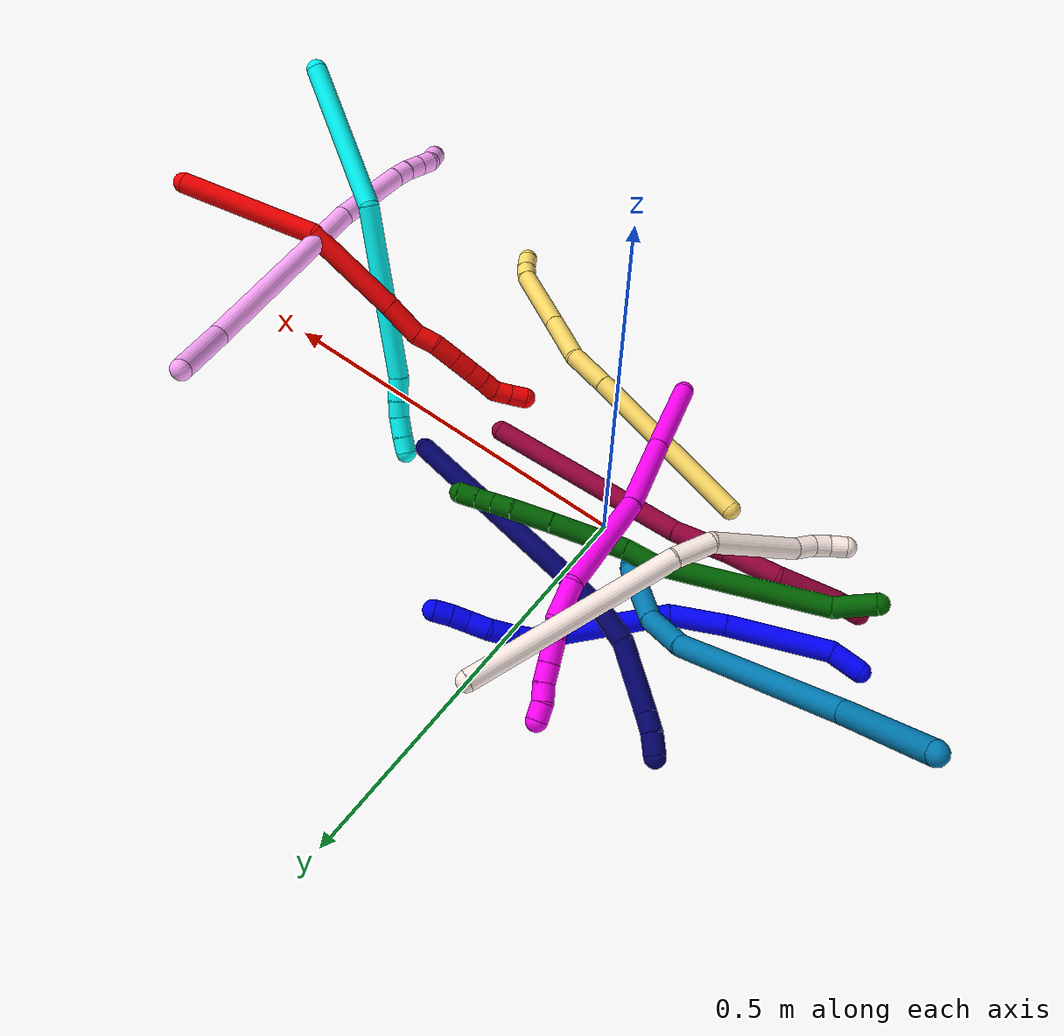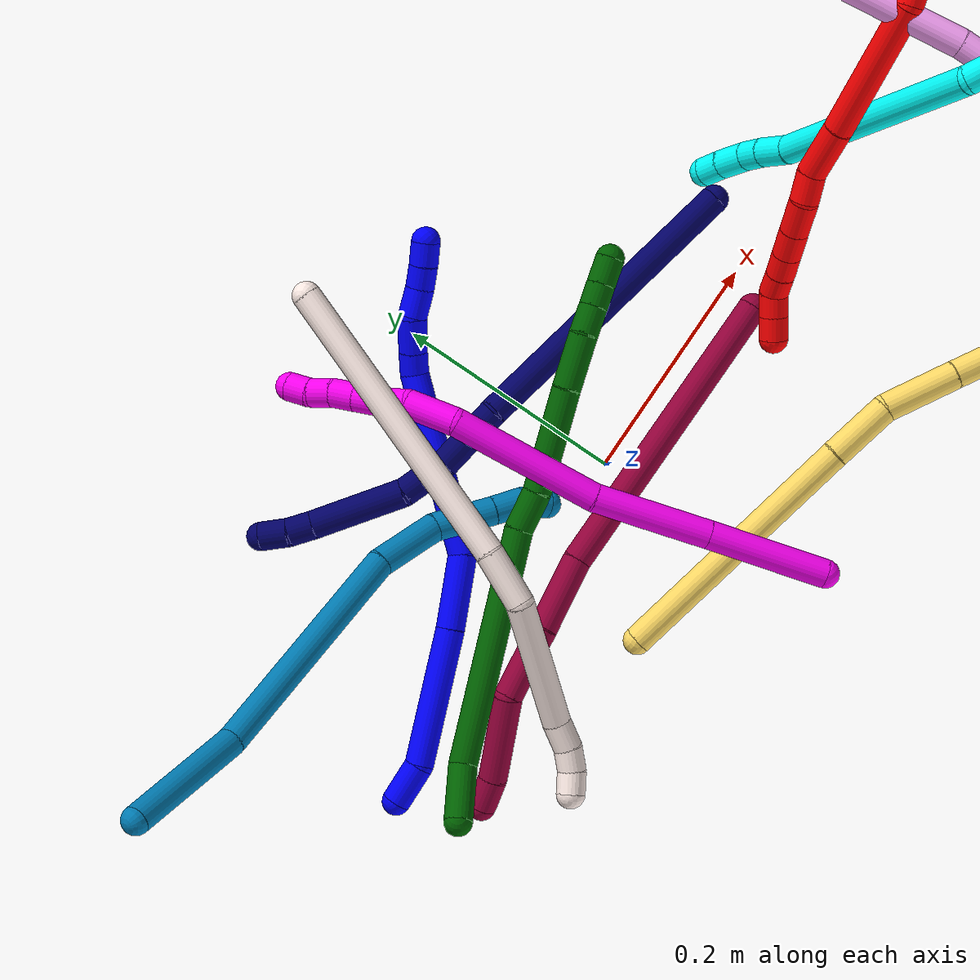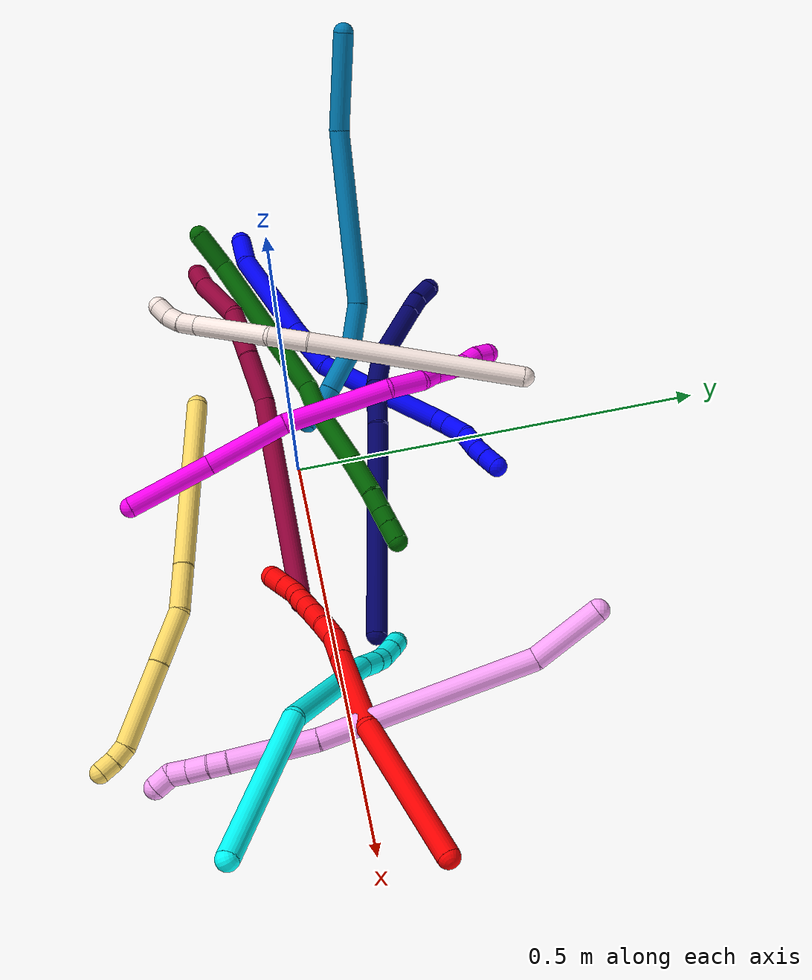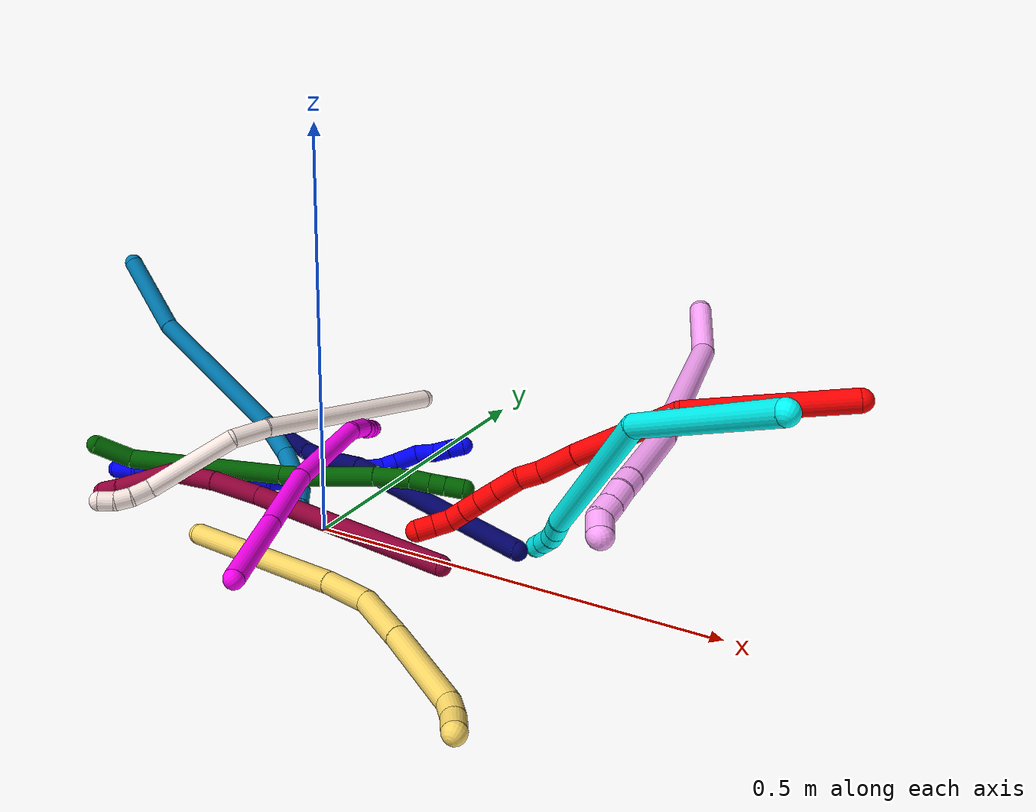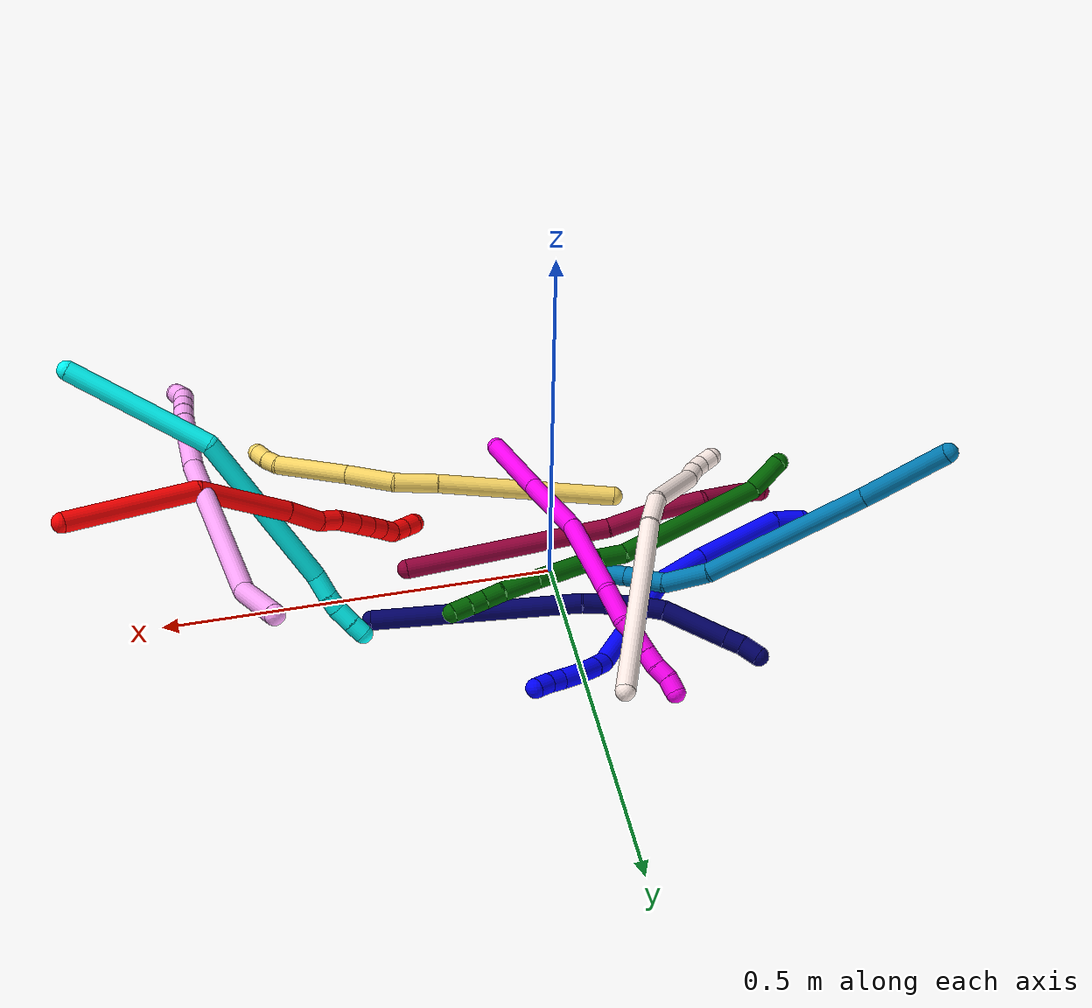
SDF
<sdf version="1.7">
 <world name="default">
  <plugin name="TubeGeneratorPlugin" filename="libtube_generator_plugin.so"/>
  <model name="photoneo_s_sensor">
   <static>1</static>
   <pose>0 0 2 1.57079 1.57079 3.14159</pose>
   <link name="link">
    <inertial><mass>0.1</mass></inertial>
    <sensor name="sensor" type="depth">
     <update_rate>30</update_rate>
     <camera>
      <horizontal_fov>1.22</horizontal_fov>
      <image><width>1920</width><height>1200</height><format>B8G8R8</format></image>
      <clip><near>0.1</near><far>4</far></clip>
      <depth_camera><output>points</output></depth_camera>
     </camera>
     <plugin name="camera_plugin" filename="libgazebo_ros_depth_camera.so">
      <baseline>0.2</baseline>
      <alwaysOn>1</alwaysOn>
      <updateRate>0.0</updateRate>
      <cameraName>camera_ir</cameraName>
      <imageTopicName>/camera/color/image_raw</imageTopicName>
      <cameraInfoTopicName>/camera/color/camera_info</cameraInfoTopicName>
      <depthImageTopicName>/camera/depth/image_raw</depthImageTopicName>
      <depthImageCameraInfoTopicName>/camera/depth/camera_info</depthImageCameraInfoTopicName>
      <pointCloudTopicName>/camera/depth/points</pointCloudTopicName>
      <frameName>fr_optical</frameName>
      <pointCloudCutoff>0.1</pointCloudCutoff>
      <pointCloudCutoffMax>2.0</pointCloudCutoffMax>
      <distortionK1>0</distortionK1>
      <distortionK2>0</distortionK2>
      <distortionK3>0</distortionK3>
      <distortionT1>0</distortionT1>
      <distortionT2>0</distortionT2>
      <CxPrime>0</CxPrime>
      <Cx>0</Cx>
      <Cy>0</Cy>
      <focalLength>0</focalLength>
      <hackBaseline>0</hackBaseline>
     </plugin>
    </sensor>
   </link>
  </model>
  <gravity>0 0 -9.8</gravity>
  <magnetic_field>6e-06 2.3e-05 -4.2e-05</magnetic_field>
  <atmosphere type="adiabatic"/>
  <physics name="default_physics" default="0" type="ode">
   <max_step_size>0.003</max_step_size>
   <real_time_factor>1</real_time_factor>
   <real_time_update_rate>1000</real_time_update_rate>
   <max_contacts>10000</max_contacts>
   <ode>
    <solver>
     <type>quick</type>
     <iters>100</iters>
     <sor>1.3</sor>
     <use_dynamic_moi_rescaling>0</use_dynamic_moi_rescaling>
    </solver>
    <constraints>
     <contact_max_correcting_vel>0</contact_max_correcting_vel>
     <contact_surface_layer>0.001</contact_surface_layer>
     <cfm>0</cfm>
     <erp>0.2</erp>
    </constraints>
   </ode>
  </physics>
  <scene><ambient>0.4 0.4 0.4 1</ambient><background>0.7 0.7 0.7 1</background><shadows>0</shadows></scene>
  <audio><device>default</device></audio>
  <spherical_coordinates>
   <surface_model>EARTH_WGS84</surface_model>
   <latitude_deg>0</latitude_deg>
   <longitude_deg>0</longitude_deg>
   <elevation>0</elevation>
   <heading_deg>0</heading_deg>
  </spherical_coordinates>
  <model name="bin">
   <static>1</static>
   <link name="bottom">
    <collision name="collision-bottom">
     <pose>0 0 -0.01 0 -0 0</pose>
     <geometry><box><size>0.8 0.6 0.02</size></box></geometry>
     <surface>
      <friction><ode><mu>100</mu><mu2>100</mu2></ode></friction>
      <contact><collide_bitmask>65535</collide_bitmask></contact>
     </surface>
    </collision>
   </link>
   <link name="west_wall">
    <collision name="collision-west_wall">
     <pose>-0.41 0 0.1 0 -0 0</pose>
     <geometry><box><size>0.02 0.6 0.2</size></box></geometry>
     <surface>
      <friction><ode><mu>100</mu><mu2>100</mu2></ode></friction>
      <contact><collide_bitmask>65535</collide_bitmask></contact>
     </surface>
    </collision>
   </link>
   <link name="east_wall">
    <collision name="collision-east_wall">
     <pose>0.41 0 0.1 0 -0 0</pose>
     <geometry><box><size>0.02 0.6 0.2</size></box></geometry>
     <surface>
      <friction><ode><mu>100</mu><mu2>100</mu2></ode></friction>
      <contact><collide_bitmask>65535</collide_bitmask></contact>
     </surface>
    </collision>
   </link>
   <link name="south_wall">
    <collision name="collision-south_wall">
     <pose>0 -0.31 0.1 0 -0 0</pose>
     <geometry><box><size>0.8 0.02 0.2</size></box></geometry>
     <surface>
      <friction><ode><mu>100</mu><mu2>100</mu2></ode></friction>
      <contact><collide_bitmask>65535</collide_bitmask></contact>
     </surface>
    </collision>
   </link>
   <link name="north_wall">
    <collision name="collision-north_wall">
     <pose>0 0.31 0.1 0 -0 0</pose>
     <geometry><box><size>0.8 0.02 0.2</size></box></geometry>
     <surface>
      <friction><ode><mu>100</mu><mu2>100</mu2></ode></friction>
      <contact><collide_bitmask>65535</collide_bitmask></contact>
     </surface>
    </collision>
   </link>
  </model>
  <model name="1">
   <static>0</static>
   <link name="1">
    <collision name="collision-cylinder-e_1_1_4">
     <pose>0.008396 -0.002607 -0.016357 2.98357 0.469124 2.50169</pose>
     <geometry><cylinder><radius>0.0125</radius><length>0.03714</length></cylinder></geometry>
     <surface>
      <friction><ode><mu>1.16</mu><mu2>1.16</mu2><slip1>0</slip1><slip2>0</slip2></ode></friction>
      <contact><ode><kp>1e+06</kp><kd>1</kd><max_vel>0</max_vel><min_depth>0.001</min_depth></ode></contact>
     </surface>
    </collision>
    <visual name="visual-cylinder-e_1_1_4">
     <pose>0.008396 -0.002607 -0.016357 2.98357 0.469124 2.50169</pose>
     <geometry><cylinder><radius>0.0125</radius><length>0.03714</length></cylinder></geometry>
     <material><ambient>0 0 1 1</ambient></material>
    </visual>
    <collision name="collision-cylinder-e_2_4_5">
     <pose>0.051893 0.00668 -0.079528 -2.89281 0.628444 -2.40702</pose>
     <geometry><cylinder><radius>0.0125</radius><length>0.119416</length></cylinder></geometry>
     <surface>
      <friction><ode><mu>1.16</mu><mu2>1.16</mu2><slip1>0</slip1><slip2>0</slip2></ode></friction>
      <contact><ode><kp>1e+06</kp><kd>1</kd><max_vel>0</max_vel><min_depth>0.001</min_depth></ode></contact>
     </surface>
    </collision>
    <visual name="visual-cylinder-e_2_4_5">
     <pose>0.051893 0.00668 -0.079528 -2.89281 0.628444 -2.40702</pose>
     <geometry><cylinder><radius>0.0125</radius><length>0.119416</length></cylinder></geometry>
     <material><ambient>0 0 1 1</ambient></material>
    </visual>
    <collision name="collision-cylinder-e_3_5_6">
     <pose>0.106765 0.026785 -0.150716 -2.8166 0.655348 -2.24285</pose>
     <geometry><cylinder><radius>0.0125</radius><length>0.064882</length></cylinder></geometry>
     <surface>
      <friction><ode><mu>1.16</mu><mu2>1.16</mu2><slip1>0</slip1><slip2>0</slip2></ode></friction>
      <contact><ode><kp>1e+06</kp><kd>1</kd><max_vel>0</max_vel><min_depth>0.001</min_depth></ode></contact>
     </surface>
    </collision>
    <visual name="visual-cylinder-e_3_5_6">
     <pose>0.106765 0.026785 -0.150716 -2.8166 0.655348 -2.24285</pose>
     <geometry><cylinder><radius>0.0125</radius><length>0.064882</length></cylinder></geometry>
     <material><ambient>0 0 1 1</ambient></material>
    </visual>
    <collision name="collision-cylinder-e_4_6_7">
     <pose>0.190973 0.069179 -0.208637 -2.34682 0.931625 -1.75026</pose>
     <geometry><cylinder><radius>0.0125</radius><length>0.160573</length></cylinder></geometry>
     <surface>
      <friction><ode><mu>1.16</mu><mu2>1.16</mu2><slip1>0</slip1><slip2>0</slip2></ode></friction>
      <contact><ode><kp>1e+06</kp><kd>1</kd><max_vel>0</max_vel><min_depth>0.001</min_depth></ode></contact>
     </surface>
    </collision>
    <visual name="visual-cylinder-e_4_6_7">
     <pose>0.190973 0.069179 -0.208637 -2.34682 0.931625 -1.75026</pose>
     <geometry><cylinder><radius>0.0125</radius><length>0.160573</length></cylinder></geometry>
     <material><ambient>0 0 1 1</ambient></material>
    </visual>
    <collision name="collision-cylinder-e_5_7_8">
     <pose>0.264336 0.103965 -0.24705 -3.01818 1.06835 -2.93346</pose>
     <geometry><cylinder><radius>0.0125</radius><length>0.020368</length></cylinder></geometry>
     <surface>
      <friction><ode><mu>1.16</mu><mu2>1.16</mu2><slip1>0</slip1><slip2>0</slip2></ode></friction>
      <contact><ode><kp>1e+06</kp><kd>1</kd><max_vel>0</max_vel><min_depth>0.001</min_depth></ode></contact>
     </surface>
    </collision>
    <visual name="visual-cylinder-e_5_7_8">
     <pose>0.264336 0.103965 -0.24705 -3.01818 1.06835 -2.93346</pose>
     <geometry><cylinder><radius>0.0125</radius><length>0.020368</length></cylinder></geometry>
     <material><ambient>0 0 1 1</ambient></material>
    </visual>
    <collision name="collision-cylinder-e_6_8_9">
     <pose>0.286703 0.104455 -0.259505 3.12671 1.05687 3.1161</pose>
     <geometry><cylinder><radius>0.0125</radius><length>0.030873</length></cylinder></geometry>
     <surface>
      <friction><ode><mu>1.16</mu><mu2>1.16</mu2><slip1>0</slip1><slip2>0</slip2></ode></friction>
      <contact><ode><kp>1e+06</kp><kd>1</kd><max_vel>0</max_vel><min_depth>0.001</min_depth></ode></contact>
     </surface>
    </collision>
    <visual name="visual-cylinder-e_6_8_9">
     <pose>0.286703 0.104455 -0.259505 3.12671 1.05687 3.1161</pose>
     <geometry><cylinder><radius>0.0125</radius><length>0.030873</length></cylinder></geometry>
     <material><ambient>0 0 1 1</ambient></material>
    </visual>
    <collision name="collision-cylinder-e_7_9_10">
     <pose>0.308739 0.104745 -0.276718 -3.09976 0.728366 -3.03195</pose>
     <geometry><cylinder><radius>0.0125</radius><length>0.025819</length></cylinder></geometry>
     <surface>
      <friction><ode><mu>1.16</mu><mu2>1.16</mu2><slip1>0</slip1><slip2>0</slip2></ode></friction>
      <contact><ode><kp>1e+06</kp><kd>1</kd><max_vel>0</max_vel><min_depth>0.001</min_depth></ode></contact>
     </surface>
    </collision>
    <visual name="visual-cylinder-e_7_9_10">
     <pose>0.308739 0.104745 -0.276718 -3.09976 0.728366 -3.03195</pose>
     <geometry><cylinder><radius>0.0125</radius><length>0.025819</length></cylinder></geometry>
     <material><ambient>0 0 1 1</ambient></material>
    </visual>
    <collision name="collision-cylinder-e_8_10_11">
     <pose>0.325206 0.104665 -0.292791 3.06672 0.883306 2.9835</pose>
     <geometry><cylinder><radius>0.0125</radius><length>0.020376</length></cylinder></geometry>
     <surface>
      <friction><ode><mu>1.16</mu><mu2>1.16</mu2><slip1>0</slip1><slip2>0</slip2></ode></friction>
      <contact><ode><kp>1e+06</kp><kd>1</kd><max_vel>0</max_vel><min_depth>0.001</min_depth></ode></contact>
     </surface>
    </collision>
    <visual name="visual-cylinder-e_8_10_11">
     <pose>0.325206 0.104665 -0.292791 3.06672 0.883306 2.9835</pose>
     <geometry><cylinder><radius>0.0125</radius><length>0.020376</length></cylinder></geometry>
     <material><ambient>0 0 1 1</ambient></material>
    </visual>
    <collision name="collision-cylinder-e_9_11_2">
     <pose>0.341149 0.104598 -0.305588 -3.07596 0.903042 -3.0064</pose>
     <geometry><cylinder><radius>0.0125</radius><length>0.020552</length></cylinder></geometry>
     <surface>
      <friction><ode><mu>1.16</mu><mu2>1.16</mu2><slip1>0</slip1><slip2>0</slip2></ode></friction>
      <contact><ode><kp>1e+06</kp><kd>1</kd><max_vel>0</max_vel><min_depth>0.001</min_depth></ode></contact>
     </surface>
    </collision>
    <visual name="visual-cylinder-e_9_11_2">
     <pose>0.341149 0.104598 -0.305588 -3.07596 0.903042 -3.0064</pose>
     <geometry><cylinder><radius>0.0125</radius><length>0.020552</length></cylinder></geometry>
     <material><ambient>0 0 1 1</ambient></material>
    </visual>
    <collision name="collision-sphere-2">
     <pose>0.349218 0.105016 -0.311937 0 -0 0</pose>
     <geometry><sphere><radius>0.0125</radius></sphere></geometry>
     <surface>
      <friction><ode><mu>1.16</mu><mu2>1.16</mu2><slip1>0</slip1><slip2>0</slip2></ode></friction>
      <contact><ode><kp>1e+06</kp><kd>1</kd><max_vel>0</max_vel><min_depth>0.001</min_depth></ode></contact>
     </surface>
    </collision>
    <visual name="visual-sphere-2">
     <pose>0.349218 0.105016 -0.311937 0 -0 0</pose>
     <geometry><sphere><radius>0.0125</radius></sphere></geometry>
     <material><ambient>0 0 1 1</ambient></material>
    </visual>
    <collision name="collision-sphere-11">
     <pose>0.33308 0.104181 -0.299238 0 -0 0</pose>
     <geometry><sphere><radius>0.0125</radius></sphere></geometry>
     <surface>
      <friction><ode><mu>1.16</mu><mu2>1.16</mu2><slip1>0</slip1><slip2>0</slip2></ode></friction>
      <contact><ode><kp>1e+06</kp><kd>1</kd><max_vel>0</max_vel><min_depth>0.001</min_depth></ode></contact>
     </surface>
    </collision>
    <visual name="visual-sphere-11">
     <pose>0.33308 0.104181 -0.299238 0 -0 0</pose>
     <geometry><sphere><radius>0.0125</radius></sphere></geometry>
     <material><ambient>0 0 1 1</ambient></material>
    </visual>
    <collision name="collision-sphere-10">
     <pose>0.317333 0.105148 -0.286344 0 -0 0</pose>
     <geometry><sphere><radius>0.0125</radius></sphere></geometry>
     <surface>
      <friction><ode><mu>1.16</mu><mu2>1.16</mu2><slip1>0</slip1><slip2>0</slip2></ode></friction>
      <contact><ode><kp>1e+06</kp><kd>1</kd><max_vel>0</max_vel><min_depth>0.001</min_depth></ode></contact>
     </surface>
    </collision>
    <visual name="visual-sphere-10">
     <pose>0.317333 0.105148 -0.286344 0 -0 0</pose>
     <geometry><sphere><radius>0.0125</radius></sphere></geometry>
     <material><ambient>0 0 1 1</ambient></material>
    </visual>
    <collision name="collision-sphere-9">
     <pose>0.300146 0.104342 -0.267093 0 -0 0</pose>
     <geometry><sphere><radius>0.0125</radius></sphere></geometry>
     <surface>
      <friction><ode><mu>1.16</mu><mu2>1.16</mu2><slip1>0</slip1><slip2>0</slip2></ode></friction>
      <contact><ode><kp>1e+06</kp><kd>1</kd><max_vel>0</max_vel><min_depth>0.001</min_depth></ode></contact>
     </surface>
    </collision>
    <visual name="visual-sphere-9">
     <pose>0.300146 0.104342 -0.267093 0 -0 0</pose>
     <geometry><sphere><radius>0.0125</radius></sphere></geometry>
     <material><ambient>0 0 1 1</ambient></material>
    </visual>
    <collision name="collision-sphere-4">
     <pose>0.016791 -0.005213 -0.032715 0 -0 0</pose>
     <geometry><sphere><radius>0.0125</radius></sphere></geometry>
     <surface>
      <friction><ode><mu>1.16</mu><mu2>1.16</mu2><slip1>0</slip1><slip2>0</slip2></ode></friction>
      <contact><ode><kp>1e+06</kp><kd>1</kd><max_vel>0</max_vel><min_depth>0.001</min_depth></ode></contact>
     </surface>
    </collision>
    <visual name="visual-sphere-4">
     <pose>0.016791 -0.005213 -0.032715 0 -0 0</pose>
     <geometry><sphere><radius>0.0125</radius></sphere></geometry>
     <material><ambient>0 0 1 1</ambient></material>
    </visual>
    <collision name="collision-sphere-1">
     <geometry><sphere><radius>0.0125</radius></sphere></geometry>
     <surface>
      <friction><ode><mu>1.16</mu><mu2>1.16</mu2><slip1>0</slip1><slip2>0</slip2></ode></friction>
      <contact><ode><kp>1e+06</kp><kd>1</kd><max_vel>0</max_vel><min_depth>0.001</min_depth></ode></contact>
     </surface>
    </collision>
    <visual name="visual-sphere-1">
     <geometry><sphere><radius>0.0125</radius></sphere></geometry>
     <material><ambient>0 0 1 1</ambient></material>
    </visual>
    <collision name="collision-sphere-8">
     <pose>0.273261 0.104568 -0.251917 0 -0 0</pose>
     <geometry><sphere><radius>0.0125</radius></sphere></geometry>
     <surface>
      <friction><ode><mu>1.16</mu><mu2>1.16</mu2><slip1>0</slip1><slip2>0</slip2></ode></friction>
      <contact><ode><kp>1e+06</kp><kd>1</kd><max_vel>0</max_vel><min_depth>0.001</min_depth></ode></contact>
     </surface>
    </collision>
    <visual name="visual-sphere-8">
     <pose>0.273261 0.104568 -0.251917 0 -0 0</pose>
     <geometry><sphere><radius>0.0125</radius></sphere></geometry>
     <material><ambient>0 0 1 1</ambient></material>
    </visual>
    <collision name="collision-sphere-5">
     <pose>0.086995 0.018572 -0.126342 0 -0 0</pose>
     <geometry><sphere><radius>0.0125</radius></sphere></geometry>
     <surface>
      <friction><ode><mu>1.16</mu><mu2>1.16</mu2><slip1>0</slip1><slip2>0</slip2></ode></friction>
      <contact><ode><kp>1e+06</kp><kd>1</kd><max_vel>0</max_vel><min_depth>0.001</min_depth></ode></contact>
     </surface>
    </collision>
    <visual name="visual-sphere-5">
     <pose>0.086995 0.018572 -0.126342 0 -0 0</pose>
     <geometry><sphere><radius>0.0125</radius></sphere></geometry>
     <material><ambient>0 0 1 1</ambient></material>
    </visual>
    <collision name="collision-sphere-6">
     <pose>0.126536 0.034998 -0.17509 0 -0 0</pose>
     <geometry><sphere><radius>0.0125</radius></sphere></geometry>
     <surface>
      <friction><ode><mu>1.16</mu><mu2>1.16</mu2><slip1>0</slip1><slip2>0</slip2></ode></friction>
      <contact><ode><kp>1e+06</kp><kd>1</kd><max_vel>0</max_vel><min_depth>0.001</min_depth></ode></contact>
     </surface>
    </collision>
    <visual name="visual-sphere-6">
     <pose>0.126536 0.034998 -0.17509 0 -0 0</pose>
     <geometry><sphere><radius>0.0125</radius></sphere></geometry>
     <material><ambient>0 0 1 1</ambient></material>
    </visual>
    <collision name="collision-sphere-7">
     <pose>0.25541 0.103361 -0.242183 0 -0 0</pose>
     <geometry><sphere><radius>0.0125</radius></sphere></geometry>
     <surface>
      <friction><ode><mu>1.16</mu><mu2>1.16</mu2><slip1>0</slip1><slip2>0</slip2></ode></friction>
      <contact><ode><kp>1e+06</kp><kd>1</kd><max_vel>0</max_vel><min_depth>0.001</min_depth></ode></contact>
     </surface>
    </collision>
    <visual name="visual-sphere-7">
     <pose>0.25541 0.103361 -0.242183 0 -0 0</pose>
     <geometry><sphere><radius>0.0125</radius></sphere></geometry>
     <material><ambient>0 0 1 1</ambient></material>
    </visual>
    <inertial>
     <pose>0.159891 0.051753 -0.171639 0 -0 0</pose>
     <mass>0.5</mass>
     <inertia>
      <ixx>-0.000419</ixx>
      <ixy>0</ixy>
      <ixz>0</ixz>
      <iyy>0.000105</iyy>
      <iyz>0</iyz>
      <izz>-0.000603</izz>
     </inertia>
    </inertial>
   </link>
   <pose>-0.339502 -0.014087 0.012146 -1.2779 -0.582114 1.13801</pose>
  </model>
  <model name="2">
   <static>0</static>
   <link name="2">
    <collision name="collision-cylinder-e_1_1_4">
     <pose>-0.023189 0.018988 -0.079342 -2.90669 -0.27694 1.73649</pose>
     <geometry><cylinder><radius>0.0125</radius><length>0.169629</length></cylinder></geometry>
     <surface>
      <friction><ode><mu>1.16</mu><mu2>1.16</mu2><slip1>0</slip1><slip2>0</slip2></ode></friction>
      <contact><ode><kp>1e+06</kp><kd>1</kd><max_vel>0</max_vel><min_depth>0.001</min_depth></ode></contact>
     </surface>
    </collision>
    <visual name="visual-cylinder-e_1_1_4">
     <pose>-0.023189 0.018988 -0.079342 -2.90669 -0.27694 1.73649</pose>
     <geometry><cylinder><radius>0.0125</radius><length>0.169629</length></cylinder></geometry>
     <material><ambient>1 0 0 1</ambient></material>
    </visual>
    <collision name="collision-cylinder-e_2_4_5">
     <pose>-0.04245 0.035373 -0.220183 3.09929 0.063738 1.96983</pose>
     <geometry><cylinder><radius>0.0125</radius><length>0.123358</length></cylinder></geometry>
     <surface>
      <friction><ode><mu>1.16</mu><mu2>1.16</mu2><slip1>0</slip1><slip2>0</slip2></ode></friction>
      <contact><ode><kp>1e+06</kp><kd>1</kd><max_vel>0</max_vel><min_depth>0.001</min_depth></ode></contact>
     </surface>
    </collision>
    <visual name="visual-cylinder-e_2_4_5">
     <pose>-0.04245 0.035373 -0.220183 3.09929 0.063738 1.96983</pose>
     <geometry><cylinder><radius>0.0125</radius><length>0.123358</length></cylinder></geometry>
     <material><ambient>1 0 0 1</ambient></material>
    </visual>
    <collision name="collision-cylinder-e_3_5_6">
     <pose>-0.035878 0.030624 -0.304625 3.04837 0.114223 1.77293</pose>
     <geometry><cylinder><radius>0.0125</radius><length>0.046388</length></cylinder></geometry>
     <surface>
      <friction><ode><mu>1.16</mu><mu2>1.16</mu2><slip1>0</slip1><slip2>0</slip2></ode></friction>
      <contact><ode><kp>1e+06</kp><kd>1</kd><max_vel>0</max_vel><min_depth>0.001</min_depth></ode></contact>
     </surface>
    </collision>
    <visual name="visual-cylinder-e_3_5_6">
     <pose>-0.035878 0.030624 -0.304625 3.04837 0.114223 1.77293</pose>
     <geometry><cylinder><radius>0.0125</radius><length>0.046388</length></cylinder></geometry>
     <material><ambient>1 0 0 1</ambient></material>
    </visual>
    <collision name="collision-cylinder-e_4_6_7">
     <pose>-0.036019 0.028513 -0.33995 -3.13883 -0.221199 3.11675</pose>
     <geometry><cylinder><radius>0.0125</radius><length>0.025383</length></cylinder></geometry>
     <surface>
      <friction><ode><mu>1.16</mu><mu2>1.16</mu2><slip1>0</slip1><slip2>0</slip2></ode></friction>
      <contact><ode><kp>1e+06</kp><kd>1</kd><max_vel>0</max_vel><min_depth>0.001</min_depth></ode></contact>
     </surface>
    </collision>
    <visual name="visual-cylinder-e_4_6_7">
     <pose>-0.036019 0.028513 -0.33995 -3.13883 -0.221199 3.11675</pose>
     <geometry><cylinder><radius>0.0125</radius><length>0.025383</length></cylinder></geometry>
     <material><ambient>1 0 0 1</ambient></material>
    </visual>
    <collision name="collision-cylinder-e_5_7_8">
     <pose>-0.039696 0.025449 -0.367116 2.93502 -0.059012 -0.554805</pose>
     <geometry><cylinder><radius>0.0125</radius><length>0.030263</length></cylinder></geometry>
     <surface>
      <friction><ode><mu>1.16</mu><mu2>1.16</mu2><slip1>0</slip1><slip2>0</slip2></ode></friction>
      <contact><ode><kp>1e+06</kp><kd>1</kd><max_vel>0</max_vel><min_depth>0.001</min_depth></ode></contact>
     </surface>
    </collision>
    <visual name="visual-cylinder-e_5_7_8">
     <pose>-0.039696 0.025449 -0.367116 2.93502 -0.059012 -0.554805</pose>
     <geometry><cylinder><radius>0.0125</radius><length>0.030263</length></cylinder></geometry>
     <material><ambient>1 0 0 1</ambient></material>
    </visual>
    <collision name="collision-cylinder-e_6_8_9">
     <pose>-0.041322 0.019716 -0.393725 2.92229 -0.06047 -0.536203</pose>
     <geometry><cylinder><radius>0.0125</radius><length>0.024274</length></cylinder></geometry>
     <surface>
      <friction><ode><mu>1.16</mu><mu2>1.16</mu2><slip1>0</slip1><slip2>0</slip2></ode></friction>
      <contact><ode><kp>1e+06</kp><kd>1</kd><max_vel>0</max_vel><min_depth>0.001</min_depth></ode></contact>
     </surface>
    </collision>
    <visual name="visual-cylinder-e_6_8_9">
     <pose>-0.041322 0.019716 -0.393725 2.92229 -0.06047 -0.536203</pose>
     <geometry><cylinder><radius>0.0125</radius><length>0.024274</length></cylinder></geometry>
     <material><ambient>1 0 0 1</ambient></material>
    </visual>
    <collision name="collision-cylinder-e_7_9_10">
     <pose>-0.042683 0.014843 -0.415602 2.9226 -0.060893 -0.540503</pose>
     <geometry><cylinder><radius>0.0125</radius><length>0.020636</length></cylinder></geometry>
     <surface>
      <friction><ode><mu>1.16</mu><mu2>1.16</mu2><slip1>0</slip1><slip2>0</slip2></ode></friction>
      <contact><ode><kp>1e+06</kp><kd>1</kd><max_vel>0</max_vel><min_depth>0.001</min_depth></ode></contact>
     </surface>
    </collision>
    <visual name="visual-cylinder-e_7_9_10">
     <pose>-0.042683 0.014843 -0.415602 2.9226 -0.060893 -0.540503</pose>
     <geometry><cylinder><radius>0.0125</radius><length>0.020636</length></cylinder></geometry>
     <material><ambient>1 0 0 1</ambient></material>
    </visual>
    <collision name="collision-cylinder-e_8_10_11">
     <pose>-0.043473 0.010333 -0.435396 2.91243 -0.016198 -0.140517</pose>
     <geometry><cylinder><radius>0.0125</radius><length>0.020006</length></cylinder></geometry>
     <surface>
      <friction><ode><mu>1.16</mu><mu2>1.16</mu2><slip1>0</slip1><slip2>0</slip2></ode></friction>
      <contact><ode><kp>1e+06</kp><kd>1</kd><max_vel>0</max_vel><min_depth>0.001</min_depth></ode></contact>
     </surface>
    </collision>
    <visual name="visual-cylinder-e_8_10_11">
     <pose>-0.043473 0.010333 -0.435396 2.91243 -0.016198 -0.140517</pose>
     <geometry><cylinder><radius>0.0125</radius><length>0.020006</length></cylinder></geometry>
     <material><ambient>1 0 0 1</ambient></material>
    </visual>
    <collision name="collision-cylinder-e_9_11_12">
     <pose>-0.048078 0.00747 -0.454077 3.07559 -0.460326 -2.86166</pose>
     <geometry><cylinder><radius>0.0125</radius><length>0.020003</length></cylinder></geometry>
     <surface>
      <friction><ode><mu>1.16</mu><mu2>1.16</mu2><slip1>0</slip1><slip2>0</slip2></ode></friction>
      <contact><ode><kp>1e+06</kp><kd>1</kd><max_vel>0</max_vel><min_depth>0.001</min_depth></ode></contact>
     </surface>
    </collision>
    <visual name="visual-cylinder-e_9_11_12">
     <pose>-0.048078 0.00747 -0.454077 3.07559 -0.460326 -2.86166</pose>
     <geometry><cylinder><radius>0.0125</radius><length>0.020003</length></cylinder></geometry>
     <material><ambient>1 0 0 1</ambient></material>
    </visual>
    <collision name="collision-cylinder-e_10_12_2">
     <pose>-0.057173 0.006464 -0.471894 3.09483 -0.482283 -2.95196</pose>
     <geometry><cylinder><radius>0.0125</radius><length>0.02006</length></cylinder></geometry>
     <surface>
      <friction><ode><mu>1.16</mu><mu2>1.16</mu2><slip1>0</slip1><slip2>0</slip2></ode></friction>
      <contact><ode><kp>1e+06</kp><kd>1</kd><max_vel>0</max_vel><min_depth>0.001</min_depth></ode></contact>
     </surface>
    </collision>
    <visual name="visual-cylinder-e_10_12_2">
     <pose>-0.057173 0.006464 -0.471894 3.09483 -0.482283 -2.95196</pose>
     <geometry><cylinder><radius>0.0125</radius><length>0.02006</length></cylinder></geometry>
     <material><ambient>1 0 0 1</ambient></material>
    </visual>
    <collision name="collision-sphere-2">
     <pose>-0.061825 0.006048 -0.48077 0 -0 0</pose>
     <geometry><sphere><radius>0.0125</radius></sphere></geometry>
     <surface>
      <friction><ode><mu>1.16</mu><mu2>1.16</mu2><slip1>0</slip1><slip2>0</slip2></ode></friction>
      <contact><ode><kp>1e+06</kp><kd>1</kd><max_vel>0</max_vel><min_depth>0.001</min_depth></ode></contact>
     </surface>
    </collision>
    <visual name="visual-sphere-2">
     <pose>-0.061825 0.006048 -0.48077 0 -0 0</pose>
     <geometry><sphere><radius>0.0125</radius></sphere></geometry>
     <material><ambient>1 0 0 1</ambient></material>
    </visual>
    <collision name="collision-sphere-12">
     <pose>-0.052521 0.006879 -0.463018 0 -0 0</pose>
     <geometry><sphere><radius>0.0125</radius></sphere></geometry>
     <surface>
      <friction><ode><mu>1.16</mu><mu2>1.16</mu2><slip1>0</slip1><slip2>0</slip2></ode></friction>
      <contact><ode><kp>1e+06</kp><kd>1</kd><max_vel>0</max_vel><min_depth>0.001</min_depth></ode></contact>
     </surface>
    </collision>
    <visual name="visual-sphere-12">
     <pose>-0.052521 0.006879 -0.463018 0 -0 0</pose>
     <geometry><sphere><radius>0.0125</radius></sphere></geometry>
     <material><ambient>1 0 0 1</ambient></material>
    </visual>
    <collision name="collision-sphere-11">
     <pose>-0.043635 0.008061 -0.445136 0 -0 0</pose>
     <geometry><sphere><radius>0.0125</radius></sphere></geometry>
     <surface>
      <friction><ode><mu>1.16</mu><mu2>1.16</mu2><slip1>0</slip1><slip2>0</slip2></ode></friction>
      <contact><ode><kp>1e+06</kp><kd>1</kd><max_vel>0</max_vel><min_depth>0.001</min_depth></ode></contact>
     </surface>
    </collision>
    <visual name="visual-sphere-11">
     <pose>-0.043635 0.008061 -0.445136 0 -0 0</pose>
     <geometry><sphere><radius>0.0125</radius></sphere></geometry>
     <material><ambient>1 0 0 1</ambient></material>
    </visual>
    <collision name="collision-sphere-10">
     <pose>-0.043311 0.012605 -0.425655 0 -0 0</pose>
     <geometry><sphere><radius>0.0125</radius></sphere></geometry>
     <surface>
      <friction><ode><mu>1.16</mu><mu2>1.16</mu2><slip1>0</slip1><slip2>0</slip2></ode></friction>
      <contact><ode><kp>1e+06</kp><kd>1</kd><max_vel>0</max_vel><min_depth>0.001</min_depth></ode></contact>
     </surface>
    </collision>
    <visual name="visual-sphere-10">
     <pose>-0.043311 0.012605 -0.425655 0 -0 0</pose>
     <geometry><sphere><radius>0.0125</radius></sphere></geometry>
     <material><ambient>1 0 0 1</ambient></material>
    </visual>
    <collision name="collision-sphere-9">
     <pose>-0.042055 0.01708 -0.405549 0 -0 0</pose>
     <geometry><sphere><radius>0.0125</radius></sphere></geometry>
     <surface>
      <friction><ode><mu>1.16</mu><mu2>1.16</mu2><slip1>0</slip1><slip2>0</slip2></ode></friction>
      <contact><ode><kp>1e+06</kp><kd>1</kd><max_vel>0</max_vel><min_depth>0.001</min_depth></ode></contact>
     </surface>
    </collision>
    <visual name="visual-sphere-9">
     <pose>-0.042055 0.01708 -0.405549 0 -0 0</pose>
     <geometry><sphere><radius>0.0125</radius></sphere></geometry>
     <material><ambient>1 0 0 1</ambient></material>
    </visual>
    <collision name="collision-sphere-4">
     <pose>-0.046379 0.037976 -0.158684 0 -0 0</pose>
     <geometry><sphere><radius>0.0125</radius></sphere></geometry>
     <surface>
      <friction><ode><mu>1.16</mu><mu2>1.16</mu2><slip1>0</slip1><slip2>0</slip2></ode></friction>
      <contact><ode><kp>1e+06</kp><kd>1</kd><max_vel>0</max_vel><min_depth>0.001</min_depth></ode></contact>
     </surface>
    </collision>
    <visual name="visual-sphere-4">
     <pose>-0.046379 0.037976 -0.158684 0 -0 0</pose>
     <geometry><sphere><radius>0.0125</radius></sphere></geometry>
     <material><ambient>1 0 0 1</ambient></material>
    </visual>
    <collision name="collision-sphere-1">
     <geometry><sphere><radius>0.0125</radius></sphere></geometry>
     <surface>
      <friction><ode><mu>1.16</mu><mu2>1.16</mu2><slip1>0</slip1><slip2>0</slip2></ode></friction>
      <contact><ode><kp>1e+06</kp><kd>1</kd><max_vel>0</max_vel><min_depth>0.001</min_depth></ode></contact>
     </surface>
    </collision>
    <visual name="visual-sphere-1">
     <geometry><sphere><radius>0.0125</radius></sphere></geometry>
     <material><ambient>1 0 0 1</ambient></material>
    </visual>
    <collision name="collision-sphere-8">
     <pose>-0.040588 0.022351 -0.3819 0 -0 0</pose>
     <geometry><sphere><radius>0.0125</radius></sphere></geometry>
     <surface>
      <friction><ode><mu>1.16</mu><mu2>1.16</mu2><slip1>0</slip1><slip2>0</slip2></ode></friction>
      <contact><ode><kp>1e+06</kp><kd>1</kd><max_vel>0</max_vel><min_depth>0.001</min_depth></ode></contact>
     </surface>
    </collision>
    <visual name="visual-sphere-8">
     <pose>-0.040588 0.022351 -0.3819 0 -0 0</pose>
     <geometry><sphere><radius>0.0125</radius></sphere></geometry>
     <material><ambient>1 0 0 1</ambient></material>
    </visual>
    <collision name="collision-sphere-5">
     <pose>-0.038521 0.032769 -0.281682 0 -0 0</pose>
     <geometry><sphere><radius>0.0125</radius></sphere></geometry>
     <surface>
      <friction><ode><mu>1.16</mu><mu2>1.16</mu2><slip1>0</slip1><slip2>0</slip2></ode></friction>
      <contact><ode><kp>1e+06</kp><kd>1</kd><max_vel>0</max_vel><min_depth>0.001</min_depth></ode></contact>
     </surface>
    </collision>
    <visual name="visual-sphere-5">
     <pose>-0.038521 0.032769 -0.281682 0 -0 0</pose>
     <geometry><sphere><radius>0.0125</radius></sphere></geometry>
     <material><ambient>1 0 0 1</ambient></material>
    </visual>
    <collision name="collision-sphere-6">
     <pose>-0.033234 0.028479 -0.327568 0 -0 0</pose>
     <geometry><sphere><radius>0.0125</radius></sphere></geometry>
     <surface>
      <friction><ode><mu>1.16</mu><mu2>1.16</mu2><slip1>0</slip1><slip2>0</slip2></ode></friction>
      <contact><ode><kp>1e+06</kp><kd>1</kd><max_vel>0</max_vel><min_depth>0.001</min_depth></ode></contact>
     </surface>
    </collision>
    <visual name="visual-sphere-6">
     <pose>-0.033234 0.028479 -0.327568 0 -0 0</pose>
     <geometry><sphere><radius>0.0125</radius></sphere></geometry>
     <material><ambient>1 0 0 1</ambient></material>
    </visual>
    <collision name="collision-sphere-7">
     <pose>-0.038803 0.028548 -0.352332 0 -0 0</pose>
     <geometry><sphere><radius>0.0125</radius></sphere></geometry>
     <surface>
      <friction><ode><mu>1.16</mu><mu2>1.16</mu2><slip1>0</slip1><slip2>0</slip2></ode></friction>
      <contact><ode><kp>1e+06</kp><kd>1</kd><max_vel>0</max_vel><min_depth>0.001</min_depth></ode></contact>
     </surface>
    </collision>
    <visual name="visual-sphere-7">
     <pose>-0.038803 0.028548 -0.352332 0 -0 0</pose>
     <geometry><sphere><radius>0.0125</radius></sphere></geometry>
     <material><ambient>1 0 0 1</ambient></material>
    </visual>
    <inertial>
     <pose>-0.035624 0.023539 -0.239767 0 -0 0</pose>
     <mass>0.5</mass>
     <inertia>
      <ixx>0.000414</ixx>
      <ixy>0</ixy>
      <ixz>0</ixz>
      <iyy>0.000702</iyy>
      <iyz>0</iyz>
      <izz>-1.6e-05</izz>
     </inertia>
    </inertial>
   </link>
   <pose>0.593774 0.060457 0.26092 1.049 0.365775 1.51322</pose>
  </model>
  <model name="3">
   <static>0</static>
   <link name="3">
    <collision name="collision-cylinder-e_1_1_4">
     <pose>-0.058626 0.071774 -0.024668 -1.90183 -0.657725 0.891998</pose>
     <geometry><cylinder><radius>0.0125</radius><length>0.191803</length></cylinder></geometry>
     <surface>
      <friction><ode><mu>1.16</mu><mu2>1.16</mu2><slip1>0</slip1><slip2>0</slip2></ode></friction>
      <contact><ode><kp>1e+06</kp><kd>1</kd><max_vel>0</max_vel><min_depth>0.001</min_depth></ode></contact>
     </surface>
    </collision>
    <visual name="visual-cylinder-e_1_1_4">
     <pose>-0.058626 0.071774 -0.024668 -1.90183 -0.657725 0.891998</pose>
     <geometry><cylinder><radius>0.0125</radius><length>0.191803</length></cylinder></geometry>
     <material><ambient>0.003922 1 0.996078 1</ambient></material>
    </visual>
    <collision name="collision-cylinder-e_2_4_5">
     <pose>-0.213618 0.188192 -0.05125 -1.61366 -1.13661 1.17585</pose>
     <geometry><cylinder><radius>0.0125</radius><length>0.212444</length></cylinder></geometry>
     <surface>
      <friction><ode><mu>1.16</mu><mu2>1.16</mu2><slip1>0</slip1><slip2>0</slip2></ode></friction>
      <contact><ode><kp>1e+06</kp><kd>1</kd><max_vel>0</max_vel><min_depth>0.001</min_depth></ode></contact>
     </surface>
    </collision>
    <visual name="visual-cylinder-e_2_4_5">
     <pose>-0.213618 0.188192 -0.05125 -1.61366 -1.13661 1.17585</pose>
     <geometry><cylinder><radius>0.0125</radius><length>0.212444</length></cylinder></geometry>
     <material><ambient>0.003922 1 0.996078 1</ambient></material>
    </visual>
    <collision name="collision-cylinder-e_3_5_6">
     <pose>-0.323715 0.237162 -0.055493 -2.06456 -1.22718 1.73462</pose>
     <geometry><cylinder><radius>0.0125</radius><length>0.029166</length></cylinder></geometry>
     <surface>
      <friction><ode><mu>1.16</mu><mu2>1.16</mu2><slip1>0</slip1><slip2>0</slip2></ode></friction>
      <contact><ode><kp>1e+06</kp><kd>1</kd><max_vel>0</max_vel><min_depth>0.001</min_depth></ode></contact>
     </surface>
    </collision>
    <visual name="visual-cylinder-e_3_5_6">
     <pose>-0.323715 0.237162 -0.055493 -2.06456 -1.22718 1.73462</pose>
     <geometry><cylinder><radius>0.0125</radius><length>0.029166</length></cylinder></geometry>
     <material><ambient>0.003922 1 0.996078 1</ambient></material>
    </visual>
    <collision name="collision-cylinder-e_4_6_7">
     <pose>-0.347109 0.245183 -0.058942 -1.86519 -1.1907 1.48007</pose>
     <geometry><cylinder><radius>0.0125</radius><length>0.020813</length></cylinder></geometry>
     <surface>
      <friction><ode><mu>1.16</mu><mu2>1.16</mu2><slip1>0</slip1><slip2>0</slip2></ode></friction>
      <contact><ode><kp>1e+06</kp><kd>1</kd><max_vel>0</max_vel><min_depth>0.001</min_depth></ode></contact>
     </surface>
    </collision>
    <visual name="visual-cylinder-e_4_6_7">
     <pose>-0.347109 0.245183 -0.058942 -1.86519 -1.1907 1.48007</pose>
     <geometry><cylinder><radius>0.0125</radius><length>0.020813</length></cylinder></geometry>
     <material><ambient>0.003922 1 0.996078 1</ambient></material>
    </visual>
    <collision name="collision-cylinder-e_5_7_8">
     <pose>-0.367483 0.255598 -0.062413 -1.90725 -0.984166 1.2939</pose>
     <geometry><cylinder><radius>0.0125</radius><length>0.025721</length></cylinder></geometry>
     <surface>
      <friction><ode><mu>1.16</mu><mu2>1.16</mu2><slip1>0</slip1><slip2>0</slip2></ode></friction>
      <contact><ode><kp>1e+06</kp><kd>1</kd><max_vel>0</max_vel><min_depth>0.001</min_depth></ode></contact>
     </surface>
    </collision>
    <visual name="visual-cylinder-e_5_7_8">
     <pose>-0.367483 0.255598 -0.062413 -1.90725 -0.984166 1.2939</pose>
     <geometry><cylinder><radius>0.0125</radius><length>0.025721</length></cylinder></geometry>
     <material><ambient>0.003922 1 0.996078 1</ambient></material>
    </visual>
    <collision name="collision-cylinder-e_6_8_2">
     <pose>-0.386374 0.267946 -0.066151 -1.81263 -0.95431 1.16677</pose>
     <geometry><cylinder><radius>0.0125</radius><length>0.020053</length></cylinder></geometry>
     <surface>
      <friction><ode><mu>1.16</mu><mu2>1.16</mu2><slip1>0</slip1><slip2>0</slip2></ode></friction>
      <contact><ode><kp>1e+06</kp><kd>1</kd><max_vel>0</max_vel><min_depth>0.001</min_depth></ode></contact>
     </surface>
    </collision>
    <visual name="visual-cylinder-e_6_8_2">
     <pose>-0.386374 0.267946 -0.066151 -1.81263 -0.95431 1.16677</pose>
     <geometry><cylinder><radius>0.0125</radius><length>0.020053</length></cylinder></geometry>
     <material><ambient>0.003922 1 0.996078 1</ambient></material>
    </visual>
    <collision name="collision-sphere-2">
     <pose>-0.394555 0.273575 -0.06754 0 -0 0</pose>
     <geometry><sphere><radius>0.0125</radius></sphere></geometry>
     <surface>
      <friction><ode><mu>1.16</mu><mu2>1.16</mu2><slip1>0</slip1><slip2>0</slip2></ode></friction>
      <contact><ode><kp>1e+06</kp><kd>1</kd><max_vel>0</max_vel><min_depth>0.001</min_depth></ode></contact>
     </surface>
    </collision>
    <visual name="visual-sphere-2">
     <pose>-0.394555 0.273575 -0.06754 0 -0 0</pose>
     <geometry><sphere><radius>0.0125</radius></sphere></geometry>
     <material><ambient>0.003922 1 0.996078 1</ambient></material>
    </visual>
    <collision name="collision-sphere-4">
     <pose>-0.117252 0.143549 -0.049335 0 -0 0</pose>
     <geometry><sphere><radius>0.0125</radius></sphere></geometry>
     <surface>
      <friction><ode><mu>1.16</mu><mu2>1.16</mu2><slip1>0</slip1><slip2>0</slip2></ode></friction>
      <contact><ode><kp>1e+06</kp><kd>1</kd><max_vel>0</max_vel><min_depth>0.001</min_depth></ode></contact>
     </surface>
    </collision>
    <visual name="visual-sphere-4">
     <pose>-0.117252 0.143549 -0.049335 0 -0 0</pose>
     <geometry><sphere><radius>0.0125</radius></sphere></geometry>
     <material><ambient>0.003922 1 0.996078 1</ambient></material>
    </visual>
    <collision name="collision-sphere-1">
     <geometry><sphere><radius>0.0125</radius></sphere></geometry>
     <surface>
      <friction><ode><mu>1.16</mu><mu2>1.16</mu2><slip1>0</slip1><slip2>0</slip2></ode></friction>
      <contact><ode><kp>1e+06</kp><kd>1</kd><max_vel>0</max_vel><min_depth>0.001</min_depth></ode></contact>
     </surface>
    </collision>
    <visual name="visual-sphere-1">
     <geometry><sphere><radius>0.0125</radius></sphere></geometry>
     <material><ambient>0.003922 1 0.996078 1</ambient></material>
    </visual>
    <collision name="collision-sphere-8">
     <pose>-0.378194 0.262318 -0.064763 0 -0 0</pose>
     <geometry><sphere><radius>0.0125</radius></sphere></geometry>
     <surface>
      <friction><ode><mu>1.16</mu><mu2>1.16</mu2><slip1>0</slip1><slip2>0</slip2></ode></friction>
      <contact><ode><kp>1e+06</kp><kd>1</kd><max_vel>0</max_vel><min_depth>0.001</min_depth></ode></contact>
     </surface>
    </collision>
    <visual name="visual-sphere-8">
     <pose>-0.378194 0.262318 -0.064763 0 -0 0</pose>
     <geometry><sphere><radius>0.0125</radius></sphere></geometry>
     <material><ambient>0.003922 1 0.996078 1</ambient></material>
    </visual>
    <collision name="collision-sphere-5">
     <pose>-0.309984 0.232836 -0.053165 0 -0 0</pose>
     <geometry><sphere><radius>0.0125</radius></sphere></geometry>
     <surface>
      <friction><ode><mu>1.16</mu><mu2>1.16</mu2><slip1>0</slip1><slip2>0</slip2></ode></friction>
      <contact><ode><kp>1e+06</kp><kd>1</kd><max_vel>0</max_vel><min_depth>0.001</min_depth></ode></contact>
     </surface>
    </collision>
    <visual name="visual-sphere-5">
     <pose>-0.309984 0.232836 -0.053165 0 -0 0</pose>
     <geometry><sphere><radius>0.0125</radius></sphere></geometry>
     <material><ambient>0.003922 1 0.996078 1</ambient></material>
    </visual>
    <collision name="collision-sphere-6">
     <pose>-0.337445 0.241488 -0.057822 0 -0 0</pose>
     <geometry><sphere><radius>0.0125</radius></sphere></geometry>
     <surface>
      <friction><ode><mu>1.16</mu><mu2>1.16</mu2><slip1>0</slip1><slip2>0</slip2></ode></friction>
      <contact><ode><kp>1e+06</kp><kd>1</kd><max_vel>0</max_vel><min_depth>0.001</min_depth></ode></contact>
     </surface>
    </collision>
    <visual name="visual-sphere-6">
     <pose>-0.337445 0.241488 -0.057822 0 -0 0</pose>
     <geometry><sphere><radius>0.0125</radius></sphere></geometry>
     <material><ambient>0.003922 1 0.996078 1</ambient></material>
    </visual>
    <collision name="collision-sphere-7">
     <pose>-0.356773 0.248878 -0.060062 0 -0 0</pose>
     <geometry><sphere><radius>0.0125</radius></sphere></geometry>
     <surface>
      <friction><ode><mu>1.16</mu><mu2>1.16</mu2><slip1>0</slip1><slip2>0</slip2></ode></friction>
      <contact><ode><kp>1e+06</kp><kd>1</kd><max_vel>0</max_vel><min_depth>0.001</min_depth></ode></contact>
     </surface>
    </collision>
    <visual name="visual-sphere-7">
     <pose>-0.356773 0.248878 -0.060062 0 -0 0</pose>
     <geometry><sphere><radius>0.0125</radius></sphere></geometry>
     <material><ambient>0.003922 1 0.996078 1</ambient></material>
    </visual>
    <inertial>
     <pose>-0.180985 0.155429 -0.042793 0 -0 0</pose>
     <mass>0.5</mass>
     <inertia><ixx>0.00108</ixx><ixy>0</ixy><ixz>0</ixz><iyy>0.001521</iyy><iyz>0</iyz><izz>0.00031</izz></inertia>
    </inertial>
   </link>
   <pose>0.566434 -0.149637 0.310898 2.99999 -1.08424 -1.37226</pose>
  </model>
  <model name="4">
   <static>0</static>
   <link name="4">
    <collision name="collision-cylinder-e_1_1_4">
     <pose>0.003263 0.02725 0.030678 -0.726291 0.07935 -0.030166</pose>
     <geometry><cylinder><radius>0.0125</radius><length>0.082325</length></cylinder></geometry>
     <surface>
      <friction><ode><mu>1.16</mu><mu2>1.16</mu2><slip1>0</slip1><slip2>0</slip2></ode></friction>
      <contact><ode><kp>1e+06</kp><kd>1</kd><max_vel>0</max_vel><min_depth>0.001</min_depth></ode></contact>
     </surface>
    </collision>
    <visual name="visual-cylinder-e_1_1_4">
     <pose>0.003263 0.02725 0.030678 -0.726291 0.07935 -0.030166</pose>
     <geometry><cylinder><radius>0.0125</radius><length>0.082325</length></cylinder></geometry>
     <material><ambient>1 0.65098 0.996078 1</ambient></material>
    </visual>
    <collision name="collision-cylinder-e_2_4_5">
     <pose>0.002414 0.097774 0.172963 -0.369889 -0.034335 0.006424</pose>
     <geometry><cylinder><radius>0.0125</radius><length>0.239548</length></cylinder></geometry>
     <surface>
      <friction><ode><mu>1.16</mu><mu2>1.16</mu2><slip1>0</slip1><slip2>0</slip2></ode></friction>
      <contact><ode><kp>1e+06</kp><kd>1</kd><max_vel>0</max_vel><min_depth>0.001</min_depth></ode></contact>
     </surface>
    </collision>
    <visual name="visual-cylinder-e_2_4_5">
     <pose>0.002414 0.097774 0.172963 -0.369889 -0.034335 0.006424</pose>
     <geometry><cylinder><radius>0.0125</radius><length>0.239548</length></cylinder></geometry>
     <material><ambient>1 0.65098 0.996078 1</ambient></material>
    </visual>
    <collision name="collision-cylinder-e_3_5_6">
     <pose>0.000347 0.154011 0.330064 -0.277586 0.043197 -0.006035</pose>
     <geometry><cylinder><radius>0.0125</radius><length>0.094696</length></cylinder></geometry>
     <surface>
      <friction><ode><mu>1.16</mu><mu2>1.16</mu2><slip1>0</slip1><slip2>0</slip2></ode></friction>
      <contact><ode><kp>1e+06</kp><kd>1</kd><max_vel>0</max_vel><min_depth>0.001</min_depth></ode></contact>
     </surface>
    </collision>
    <visual name="visual-cylinder-e_3_5_6">
     <pose>0.000347 0.154011 0.330064 -0.277586 0.043197 -0.006035</pose>
     <geometry><cylinder><radius>0.0125</radius><length>0.094696</length></cylinder></geometry>
     <material><ambient>1 0.65098 0.996078 1</ambient></material>
    </visual>
    <collision name="collision-cylinder-e_4_6_7">
     <pose>0.003794 0.169753 0.385359 -0.2762 0.13675 -0.019035</pose>
     <geometry><cylinder><radius>0.0125</radius><length>0.02057</length></cylinder></geometry>
     <surface>
      <friction><ode><mu>1.16</mu><mu2>1.16</mu2><slip1>0</slip1><slip2>0</slip2></ode></friction>
      <contact><ode><kp>1e+06</kp><kd>1</kd><max_vel>0</max_vel><min_depth>0.001</min_depth></ode></contact>
     </surface>
    </collision>
    <visual name="visual-cylinder-e_4_6_7">
     <pose>0.003794 0.169753 0.385359 -0.2762 0.13675 -0.019035</pose>
     <geometry><cylinder><radius>0.0125</radius><length>0.02057</length></cylinder></geometry>
     <material><ambient>1 0.65098 0.996078 1</ambient></material>
    </visual>
    <collision name="collision-cylinder-e_5_7_8">
     <pose>0.008019 0.176225 0.405344 -0.347992 0.254963 -0.045052</pose>
     <geometry><cylinder><radius>0.0125</radius><length>0.022386</length></cylinder></geometry>
     <surface>
      <friction><ode><mu>1.16</mu><mu2>1.16</mu2><slip1>0</slip1><slip2>0</slip2></ode></friction>
      <contact><ode><kp>1e+06</kp><kd>1</kd><max_vel>0</max_vel><min_depth>0.001</min_depth></ode></contact>
     </surface>
    </collision>
    <visual name="visual-cylinder-e_5_7_8">
     <pose>0.008019 0.176225 0.405344 -0.347992 0.254963 -0.045052</pose>
     <geometry><cylinder><radius>0.0125</radius><length>0.022386</length></cylinder></geometry>
     <material><ambient>1 0.65098 0.996078 1</ambient></material>
    </visual>
    <collision name="collision-cylinder-e_6_8_9">
     <pose>0.013369 0.182835 0.424979 -0.299271 0.250069 -0.037894</pose>
     <geometry><cylinder><radius>0.0125</radius><length>0.020421</length></cylinder></geometry>
     <surface>
      <friction><ode><mu>1.16</mu><mu2>1.16</mu2><slip1>0</slip1><slip2>0</slip2></ode></friction>
      <contact><ode><kp>1e+06</kp><kd>1</kd><max_vel>0</max_vel><min_depth>0.001</min_depth></ode></contact>
     </surface>
    </collision>
    <visual name="visual-cylinder-e_6_8_9">
     <pose>0.013369 0.182835 0.424979 -0.299271 0.250069 -0.037894</pose>
     <geometry><cylinder><radius>0.0125</radius><length>0.020421</length></cylinder></geometry>
     <material><ambient>1 0.65098 0.996078 1</ambient></material>
    </visual>
    <collision name="collision-cylinder-e_7_9_2">
     <pose>0.01605 0.19264 0.441717 -0.757424 0.015378 -0.006119</pose>
     <geometry><cylinder><radius>0.0125</radius><length>0.020055</length></cylinder></geometry>
     <surface>
      <friction><ode><mu>1.16</mu><mu2>1.16</mu2><slip1>0</slip1><slip2>0</slip2></ode></friction>
      <contact><ode><kp>1e+06</kp><kd>1</kd><max_vel>0</max_vel><min_depth>0.001</min_depth></ode></contact>
     </surface>
    </collision>
    <visual name="visual-cylinder-e_7_9_2">
     <pose>0.01605 0.19264 0.441717 -0.757424 0.015378 -0.006119</pose>
     <geometry><cylinder><radius>0.0125</radius><length>0.020055</length></cylinder></geometry>
     <material><ambient>1 0.65098 0.996078 1</ambient></material>
    </visual>
    <collision name="collision-sphere-2">
     <pose>0.016204 0.199529 0.449002 0 -0 0</pose>
     <geometry><sphere><radius>0.0125</radius></sphere></geometry>
     <surface>
      <friction><ode><mu>1.16</mu><mu2>1.16</mu2><slip1>0</slip1><slip2>0</slip2></ode></friction>
      <contact><ode><kp>1e+06</kp><kd>1</kd><max_vel>0</max_vel><min_depth>0.001</min_depth></ode></contact>
     </surface>
    </collision>
    <visual name="visual-sphere-2">
     <pose>0.016204 0.199529 0.449002 0 -0 0</pose>
     <geometry><sphere><radius>0.0125</radius></sphere></geometry>
     <material><ambient>1 0.65098 0.996078 1</ambient></material>
    </visual>
    <collision name="collision-sphere-9">
     <pose>0.015895 0.185751 0.434432 0 -0 0</pose>
     <geometry><sphere><radius>0.0125</radius></sphere></geometry>
     <surface>
      <friction><ode><mu>1.16</mu><mu2>1.16</mu2><slip1>0</slip1><slip2>0</slip2></ode></friction>
      <contact><ode><kp>1e+06</kp><kd>1</kd><max_vel>0</max_vel><min_depth>0.001</min_depth></ode></contact>
     </surface>
    </collision>
    <visual name="visual-sphere-9">
     <pose>0.015895 0.185751 0.434432 0 -0 0</pose>
     <geometry><sphere><radius>0.0125</radius></sphere></geometry>
     <material><ambient>1 0.65098 0.996078 1</ambient></material>
    </visual>
    <collision name="collision-sphere-4">
     <pose>0.006526 0.0545 0.061356 0 -0 0</pose>
     <geometry><sphere><radius>0.0125</radius></sphere></geometry>
     <surface>
      <friction><ode><mu>1.16</mu><mu2>1.16</mu2><slip1>0</slip1><slip2>0</slip2></ode></friction>
      <contact><ode><kp>1e+06</kp><kd>1</kd><max_vel>0</max_vel><min_depth>0.001</min_depth></ode></contact>
     </surface>
    </collision>
    <visual name="visual-sphere-4">
     <pose>0.006526 0.0545 0.061356 0 -0 0</pose>
     <geometry><sphere><radius>0.0125</radius></sphere></geometry>
     <material><ambient>1 0.65098 0.996078 1</ambient></material>
    </visual>
    <collision name="collision-sphere-1">
     <geometry><sphere><radius>0.0125</radius></sphere></geometry>
     <surface>
      <friction><ode><mu>1.16</mu><mu2>1.16</mu2><slip1>0</slip1><slip2>0</slip2></ode></friction>
      <contact><ode><kp>1e+06</kp><kd>1</kd><max_vel>0</max_vel><min_depth>0.001</min_depth></ode></contact>
     </surface>
    </collision>
    <visual name="visual-sphere-1">
     <geometry><sphere><radius>0.0125</radius></sphere></geometry>
     <material><ambient>1 0.65098 0.996078 1</ambient></material>
    </visual>
    <collision name="collision-sphere-8">
     <pose>0.010842 0.179918 0.415526 0 -0 0</pose>
     <geometry><sphere><radius>0.0125</radius></sphere></geometry>
     <surface>
      <friction><ode><mu>1.16</mu><mu2>1.16</mu2><slip1>0</slip1><slip2>0</slip2></ode></friction>
      <contact><ode><kp>1e+06</kp><kd>1</kd><max_vel>0</max_vel><min_depth>0.001</min_depth></ode></contact>
     </surface>
    </collision>
    <visual name="visual-sphere-8">
     <pose>0.010842 0.179918 0.415526 0 -0 0</pose>
     <geometry><sphere><radius>0.0125</radius></sphere></geometry>
     <material><ambient>1 0.65098 0.996078 1</ambient></material>
    </visual>
    <collision name="collision-sphere-5">
     <pose>-0.001698 0.141048 0.284571 0 -0 0</pose>
     <geometry><sphere><radius>0.0125</radius></sphere></geometry>
     <surface>
      <friction><ode><mu>1.16</mu><mu2>1.16</mu2><slip1>0</slip1><slip2>0</slip2></ode></friction>
      <contact><ode><kp>1e+06</kp><kd>1</kd><max_vel>0</max_vel><min_depth>0.001</min_depth></ode></contact>
     </surface>
    </collision>
    <visual name="visual-sphere-5">
     <pose>-0.001698 0.141048 0.284571 0 -0 0</pose>
     <geometry><sphere><radius>0.0125</radius></sphere></geometry>
     <material><ambient>1 0.65098 0.996078 1</ambient></material>
    </visual>
    <collision name="collision-sphere-6">
     <pose>0.002392 0.166974 0.375556 0 -0 0</pose>
     <geometry><sphere><radius>0.0125</radius></sphere></geometry>
     <surface>
      <friction><ode><mu>1.16</mu><mu2>1.16</mu2><slip1>0</slip1><slip2>0</slip2></ode></friction>
      <contact><ode><kp>1e+06</kp><kd>1</kd><max_vel>0</max_vel><min_depth>0.001</min_depth></ode></contact>
     </surface>
    </collision>
    <visual name="visual-sphere-6">
     <pose>0.002392 0.166974 0.375556 0 -0 0</pose>
     <geometry><sphere><radius>0.0125</radius></sphere></geometry>
     <material><ambient>1 0.65098 0.996078 1</ambient></material>
    </visual>
    <collision name="collision-sphere-7">
     <pose>0.005196 0.172531 0.395162 0 -0 0</pose>
     <geometry><sphere><radius>0.0125</radius></sphere></geometry>
     <surface>
      <friction><ode><mu>1.16</mu><mu2>1.16</mu2><slip1>0</slip1><slip2>0</slip2></ode></friction>
      <contact><ode><kp>1e+06</kp><kd>1</kd><max_vel>0</max_vel><min_depth>0.001</min_depth></ode></contact>
     </surface>
    </collision>
    <visual name="visual-sphere-7">
     <pose>0.005196 0.172531 0.395162 0 -0 0</pose>
     <geometry><sphere><radius>0.0125</radius></sphere></geometry>
     <material><ambient>1 0.65098 0.996078 1</ambient></material>
    </visual>
    <inertial>
     <pose>0.003464 0.110566 0.219504 0 -0 0</pose>
     <mass>0.5</mass>
     <inertia>
      <ixx>0.001291</ixx>
      <ixy>0</ixy>
      <ixz>0</ixz>
      <iyy>0.001212</iyy>
      <iyz>0</iyz>
      <izz>-0.000406</izz>
     </inertia>
    </inertial>
   </link>
   <pose>0.373916 0.266317 0.272242 -1.35851 0.898702 3.13613</pose>
  </model>
  <model name="5">
   <static>0</static>
   <link name="5">
    <collision name="collision-cylinder-e_1_1_4">
     <pose>0.112079 0.000285 -0.030842 -3.13237 1.30225 -3.12949</pose>
     <geometry><cylinder><radius>0.0125</radius><length>0.23249</length></cylinder></geometry>
     <surface>
      <friction><ode><mu>1.16</mu><mu2>1.16</mu2><slip1>0</slip1><slip2>0</slip2></ode></friction>
      <contact><ode><kp>1e+06</kp><kd>1</kd><max_vel>0</max_vel><min_depth>0.001</min_depth></ode></contact>
     </surface>
    </collision>
    <visual name="visual-cylinder-e_1_1_4">
     <pose>0.112079 0.000285 -0.030842 -3.13237 1.30225 -3.12949</pose>
     <geometry><cylinder><radius>0.0125</radius><length>0.23249</length></cylinder></geometry>
     <material><ambient>1 0.858824 0.4 1</ambient></material>
    </visual>
    <collision name="collision-cylinder-e_2_4_5">
     <pose>0.251601 0.002656 -0.070521 -2.90963 1.25132 -2.82184</pose>
     <geometry><cylinder><radius>0.0125</radius><length>0.057814</length></cylinder></geometry>
     <surface>
      <friction><ode><mu>1.16</mu><mu2>1.16</mu2><slip1>0</slip1><slip2>0</slip2></ode></friction>
      <contact><ode><kp>1e+06</kp><kd>1</kd><max_vel>0</max_vel><min_depth>0.001</min_depth></ode></contact>
     </surface>
    </collision>
    <visual name="visual-cylinder-e_2_4_5">
     <pose>0.251601 0.002656 -0.070521 -2.90963 1.25132 -2.82184</pose>
     <geometry><cylinder><radius>0.0125</radius><length>0.057814</length></cylinder></geometry>
     <material><ambient>1 0.858824 0.4 1</ambient></material>
    </visual>
    <collision name="collision-cylinder-e_3_5_6">
     <pose>0.306134 0.006552 -0.098821 -3.04893 0.945692 -2.96082</pose>
     <geometry><cylinder><radius>0.0125</radius><length>0.066812</length></cylinder></geometry>
     <surface>
      <friction><ode><mu>1.16</mu><mu2>1.16</mu2><slip1>0</slip1><slip2>0</slip2></ode></friction>
      <contact><ode><kp>1e+06</kp><kd>1</kd><max_vel>0</max_vel><min_depth>0.001</min_depth></ode></contact>
     </surface>
    </collision>
    <visual name="visual-cylinder-e_3_5_6">
     <pose>0.306134 0.006552 -0.098821 -3.04893 0.945692 -2.96082</pose>
     <geometry><cylinder><radius>0.0125</radius><length>0.066812</length></cylinder></geometry>
     <material><ambient>1 0.858824 0.4 1</ambient></material>
    </visual>
    <collision name="collision-cylinder-e_4_6_7">
     <pose>0.373947 0.013274 -0.149294 -2.98447 0.914033 -2.8241</pose>
     <geometry><cylinder><radius>0.0125</radius><length>0.102842</length></cylinder></geometry>
     <surface>
      <friction><ode><mu>1.16</mu><mu2>1.16</mu2><slip1>0</slip1><slip2>0</slip2></ode></friction>
      <contact><ode><kp>1e+06</kp><kd>1</kd><max_vel>0</max_vel><min_depth>0.001</min_depth></ode></contact>
     </surface>
    </collision>
    <visual name="visual-cylinder-e_4_6_7">
     <pose>0.373947 0.013274 -0.149294 -2.98447 0.914033 -2.8241</pose>
     <geometry><cylinder><radius>0.0125</radius><length>0.102842</length></cylinder></geometry>
     <material><ambient>1 0.858824 0.4 1</ambient></material>
    </visual>
    <collision name="collision-cylinder-e_5_7_8">
     <pose>0.420632 0.017815 -0.18835 3.09553 0.637075 3.00212</pose>
     <geometry><cylinder><radius>0.0125</radius><length>0.020042</length></cylinder></geometry>
     <surface>
      <friction><ode><mu>1.16</mu><mu2>1.16</mu2><slip1>0</slip1><slip2>0</slip2></ode></friction>
      <contact><ode><kp>1e+06</kp><kd>1</kd><max_vel>0</max_vel><min_depth>0.001</min_depth></ode></contact>
     </surface>
    </collision>
    <visual name="visual-cylinder-e_5_7_8">
     <pose>0.420632 0.017815 -0.18835 3.09553 0.637075 3.00212</pose>
     <geometry><cylinder><radius>0.0125</radius><length>0.020042</length></cylinder></geometry>
     <material><ambient>1 0.858824 0.4 1</ambient></material>
    </visual>
    <collision name="collision-cylinder-e_6_8_2">
     <pose>0.431296 0.015868 -0.20508 2.962 0.489644 2.44977</pose>
     <geometry><cylinder><radius>0.0125</radius><length>0.02</length></cylinder></geometry>
     <surface>
      <friction><ode><mu>1.16</mu><mu2>1.16</mu2><slip1>0</slip1><slip2>0</slip2></ode></friction>
      <contact><ode><kp>1e+06</kp><kd>1</kd><max_vel>0</max_vel><min_depth>0.001</min_depth></ode></contact>
     </surface>
    </collision>
    <visual name="visual-cylinder-e_6_8_2">
     <pose>0.431296 0.015868 -0.20508 2.962 0.489644 2.44977</pose>
     <geometry><cylinder><radius>0.0125</radius><length>0.02</length></cylinder></geometry>
     <material><ambient>1 0.858824 0.4 1</ambient></material>
    </visual>
    <collision name="collision-sphere-2">
     <pose>0.435999 0.014292 -0.213763 0 -0 0</pose>
     <geometry><sphere><radius>0.0125</radius></sphere></geometry>
     <surface>
      <friction><ode><mu>1.16</mu><mu2>1.16</mu2><slip1>0</slip1><slip2>0</slip2></ode></friction>
      <contact><ode><kp>1e+06</kp><kd>1</kd><max_vel>0</max_vel><min_depth>0.001</min_depth></ode></contact>
     </surface>
    </collision>
    <visual name="visual-sphere-2">
     <pose>0.435999 0.014292 -0.213763 0 -0 0</pose>
     <geometry><sphere><radius>0.0125</radius></sphere></geometry>
     <material><ambient>1 0.858824 0.4 1</ambient></material>
    </visual>
    <collision name="collision-sphere-4">
     <pose>0.224157 0.000569 -0.061685 0 -0 0</pose>
     <geometry><sphere><radius>0.0125</radius></sphere></geometry>
     <surface>
      <friction><ode><mu>1.16</mu><mu2>1.16</mu2><slip1>0</slip1><slip2>0</slip2></ode></friction>
      <contact><ode><kp>1e+06</kp><kd>1</kd><max_vel>0</max_vel><min_depth>0.001</min_depth></ode></contact>
     </surface>
    </collision>
    <visual name="visual-sphere-4">
     <pose>0.224157 0.000569 -0.061685 0 -0 0</pose>
     <geometry><sphere><radius>0.0125</radius></sphere></geometry>
     <material><ambient>1 0.858824 0.4 1</ambient></material>
    </visual>
    <collision name="collision-sphere-1">
     <geometry><sphere><radius>0.0125</radius></sphere></geometry>
     <surface>
      <friction><ode><mu>1.16</mu><mu2>1.16</mu2><slip1>0</slip1><slip2>0</slip2></ode></friction>
      <contact><ode><kp>1e+06</kp><kd>1</kd><max_vel>0</max_vel><min_depth>0.001</min_depth></ode></contact>
     </surface>
    </collision>
    <visual name="visual-sphere-1">
     <geometry><sphere><radius>0.0125</radius></sphere></geometry>
     <material><ambient>1 0.858824 0.4 1</ambient></material>
    </visual>
    <collision name="collision-sphere-8">
     <pose>0.426593 0.017444 -0.196397 0 -0 0</pose>
     <geometry><sphere><radius>0.0125</radius></sphere></geometry>
     <surface>
      <friction><ode><mu>1.16</mu><mu2>1.16</mu2><slip1>0</slip1><slip2>0</slip2></ode></friction>
      <contact><ode><kp>1e+06</kp><kd>1</kd><max_vel>0</max_vel><min_depth>0.001</min_depth></ode></contact>
     </surface>
    </collision>
    <visual name="visual-sphere-8">
     <pose>0.426593 0.017444 -0.196397 0 -0 0</pose>
     <geometry><sphere><radius>0.0125</radius></sphere></geometry>
     <material><ambient>1 0.858824 0.4 1</ambient></material>
    </visual>
    <collision name="collision-sphere-5">
     <pose>0.279045 0.004743 -0.079356 0 -0 0</pose>
     <geometry><sphere><radius>0.0125</radius></sphere></geometry>
     <surface>
      <friction><ode><mu>1.16</mu><mu2>1.16</mu2><slip1>0</slip1><slip2>0</slip2></ode></friction>
      <contact><ode><kp>1e+06</kp><kd>1</kd><max_vel>0</max_vel><min_depth>0.001</min_depth></ode></contact>
     </surface>
    </collision>
    <visual name="visual-sphere-5">
     <pose>0.279045 0.004743 -0.079356 0 -0 0</pose>
     <geometry><sphere><radius>0.0125</radius></sphere></geometry>
     <material><ambient>1 0.858824 0.4 1</ambient></material>
    </visual>
    <collision name="collision-sphere-6">
     <pose>0.333223 0.008361 -0.118286 0 -0 0</pose>
     <geometry><sphere><radius>0.0125</radius></sphere></geometry>
     <surface>
      <friction><ode><mu>1.16</mu><mu2>1.16</mu2><slip1>0</slip1><slip2>0</slip2></ode></friction>
      <contact><ode><kp>1e+06</kp><kd>1</kd><max_vel>0</max_vel><min_depth>0.001</min_depth></ode></contact>
     </surface>
    </collision>
    <visual name="visual-sphere-6">
     <pose>0.333223 0.008361 -0.118286 0 -0 0</pose>
     <geometry><sphere><radius>0.0125</radius></sphere></geometry>
     <material><ambient>1 0.858824 0.4 1</ambient></material>
    </visual>
    <collision name="collision-sphere-7">
     <pose>0.414671 0.018186 -0.180303 0 -0 0</pose>
     <geometry><sphere><radius>0.0125</radius></sphere></geometry>
     <surface>
      <friction><ode><mu>1.16</mu><mu2>1.16</mu2><slip1>0</slip1><slip2>0</slip2></ode></friction>
      <contact><ode><kp>1e+06</kp><kd>1</kd><max_vel>0</max_vel><min_depth>0.001</min_depth></ode></contact>
     </surface>
    </collision>
    <visual name="visual-sphere-7">
     <pose>0.414671 0.018186 -0.180303 0 -0 0</pose>
     <geometry><sphere><radius>0.0125</radius></sphere></geometry>
     <material><ambient>1 0.858824 0.4 1</ambient></material>
    </visual>
    <inertial>
     <pose>0.233141 0.005394 -0.082161 0 -0 0</pose>
     <mass>0.5</mass>
     <inertia>
      <ixx>-0.00035</ixx>
      <ixy>0</ixy>
      <ixz>0</ixz>
      <iyy>0.001173</iyy>
      <iyz>0</iyz>
      <izz>-0.001166</izz>
     </inertia>
    </inertial>
   </link>
   <pose>-0.10923 -0.107559 0.011934 -1.25941 -0.180648 0.042478</pose>
  </model>
  <model name="6">
   <static>0</static>
   <link name="6">
    <collision name="collision-cylinder-e_1_1_4">
     <pose>0.0241 0.007156 0.002798 -1.19805 1.26214 -0.925524</pose>
     <geometry><cylinder><radius>0.0125</radius><length>0.05059</length></cylinder></geometry>
     <surface>
      <friction><ode><mu>1.16</mu><mu2>1.16</mu2><slip1>0</slip1><slip2>0</slip2></ode></friction>
      <contact><ode><kp>1e+06</kp><kd>1</kd><max_vel>0</max_vel><min_depth>0.001</min_depth></ode></contact>
     </surface>
    </collision>
    <visual name="visual-cylinder-e_1_1_4">
     <pose>0.0241 0.007156 0.002798 -1.19805 1.26214 -0.925524</pose>
     <geometry><cylinder><radius>0.0125</radius><length>0.05059</length></cylinder></geometry>
     <material><ambient>0 0.392157 0.003922 1</ambient></material>
    </visual>
    <collision name="collision-cylinder-e_2_4_5">
     <pose>0.139853 0.022752 0.051272 -0.182702 1.10174 -0.112429</pose>
     <geometry><cylinder><radius>0.0125</radius><length>0.205503</length></cylinder></geometry>
     <surface>
      <friction><ode><mu>1.16</mu><mu2>1.16</mu2><slip1>0</slip1><slip2>0</slip2></ode></friction>
      <contact><ode><kp>1e+06</kp><kd>1</kd><max_vel>0</max_vel><min_depth>0.001</min_depth></ode></contact>
     </surface>
    </collision>
    <visual name="visual-cylinder-e_2_4_5">
     <pose>0.139853 0.022752 0.051272 -0.182702 1.10174 -0.112429</pose>
     <geometry><cylinder><radius>0.0125</radius><length>0.205503</length></cylinder></geometry>
     <material><ambient>0 0.392157 0.003922 1</ambient></material>
    </visual>
    <collision name="collision-cylinder-e_3_5_6">
     <pose>0.246527 0.028349 0.106234 0.296954 0.996801 0.162451</pose>
     <geometry><cylinder><radius>0.0125</radius><length>0.035775</length></cylinder></geometry>
     <surface>
      <friction><ode><mu>1.16</mu><mu2>1.16</mu2><slip1>0</slip1><slip2>0</slip2></ode></friction>
      <contact><ode><kp>1e+06</kp><kd>1</kd><max_vel>0</max_vel><min_depth>0.001</min_depth></ode></contact>
     </surface>
    </collision>
    <visual name="visual-cylinder-e_3_5_6">
     <pose>0.246527 0.028349 0.106234 0.296954 0.996801 0.162451</pose>
     <geometry><cylinder><radius>0.0125</radius><length>0.035775</length></cylinder></geometry>
     <material><ambient>0 0.392157 0.003922 1</ambient></material>
    </visual>
    <collision name="collision-cylinder-e_4_6_7">
     <pose>0.299352 0.026126 0.140718 -0.024591 0.982775 -0.013161</pose>
     <geometry><cylinder><radius>0.0125</radius><length>0.090871</length></cylinder></geometry>
     <surface>
      <friction><ode><mu>1.16</mu><mu2>1.16</mu2><slip1>0</slip1><slip2>0</slip2></ode></friction>
      <contact><ode><kp>1e+06</kp><kd>1</kd><max_vel>0</max_vel><min_depth>0.001</min_depth></ode></contact>
     </surface>
    </collision>
    <visual name="visual-cylinder-e_4_6_7">
     <pose>0.299352 0.026126 0.140718 -0.024591 0.982775 -0.013161</pose>
     <geometry><cylinder><radius>0.0125</radius><length>0.090871</length></cylinder></geometry>
     <material><ambient>0 0.392157 0.003922 1</ambient></material>
    </visual>
    <collision name="collision-cylinder-e_5_7_8">
     <pose>0.358012 0.026733 0.177787 0.00111 1.05324 0.000645</pose>
     <geometry><cylinder><radius>0.0125</radius><length>0.047996</length></cylinder></geometry>
     <surface>
      <friction><ode><mu>1.16</mu><mu2>1.16</mu2><slip1>0</slip1><slip2>0</slip2></ode></friction>
      <contact><ode><kp>1e+06</kp><kd>1</kd><max_vel>0</max_vel><min_depth>0.001</min_depth></ode></contact>
     </surface>
    </collision>
    <visual name="visual-cylinder-e_5_7_8">
     <pose>0.358012 0.026733 0.177787 0.00111 1.05324 0.000645</pose>
     <geometry><cylinder><radius>0.0125</radius><length>0.047996</length></cylinder></geometry>
     <material><ambient>0 0.392157 0.003922 1</ambient></material>
    </visual>
    <collision name="collision-cylinder-e_6_8_9">
     <pose>0.390584 0.026584 0.194286 0.029368 1.19469 0.019978</pose>
     <geometry><cylinder><radius>0.0125</radius><length>0.025195</length></cylinder></geometry>
     <surface>
      <friction><ode><mu>1.16</mu><mu2>1.16</mu2><slip1>0</slip1><slip2>0</slip2></ode></friction>
      <contact><ode><kp>1e+06</kp><kd>1</kd><max_vel>0</max_vel><min_depth>0.001</min_depth></ode></contact>
     </surface>
    </collision>
    <visual name="visual-cylinder-e_6_8_9">
     <pose>0.390584 0.026584 0.194286 0.029368 1.19469 0.019978</pose>
     <geometry><cylinder><radius>0.0125</radius><length>0.025195</length></cylinder></geometry>
     <material><ambient>0 0.392157 0.003922 1</ambient></material>
    </visual>
    <collision name="collision-cylinder-e_7_9_10">
     <pose>0.411496 0.02635 0.202994 0.023911 1.15279 0.015543</pose>
     <geometry><cylinder><radius>0.0125</radius><length>0.020123</length></cylinder></geometry>
     <surface>
      <friction><ode><mu>1.16</mu><mu2>1.16</mu2><slip1>0</slip1><slip2>0</slip2></ode></friction>
      <contact><ode><kp>1e+06</kp><kd>1</kd><max_vel>0</max_vel><min_depth>0.001</min_depth></ode></contact>
     </surface>
    </collision>
    <visual name="visual-cylinder-e_7_9_10">
     <pose>0.411496 0.02635 0.202994 0.023911 1.15279 0.015543</pose>
     <geometry><cylinder><radius>0.0125</radius><length>0.020123</length></cylinder></geometry>
     <material><ambient>0 0.392157 0.003922 1</ambient></material>
    </visual>
    <collision name="collision-cylinder-e_8_10_2">
     <pose>0.431653 0.026073 0.21189 0.037338 1.15683 0.02438</pose>
     <geometry><cylinder><radius>0.0125</radius><length>0.023948</length></cylinder></geometry>
     <surface>
      <friction><ode><mu>1.16</mu><mu2>1.16</mu2><slip1>0</slip1><slip2>0</slip2></ode></friction>
      <contact><ode><kp>1e+06</kp><kd>1</kd><max_vel>0</max_vel><min_depth>0.001</min_depth></ode></contact>
     </surface>
    </collision>
    <visual name="visual-cylinder-e_8_10_2">
     <pose>0.431653 0.026073 0.21189 0.037338 1.15683 0.02438</pose>
     <geometry><cylinder><radius>0.0125</radius><length>0.023948</length></cylinder></geometry>
     <material><ambient>0 0.392157 0.003922 1</ambient></material>
    </visual>
    <collision name="collision-sphere-2">
     <pose>0.442616 0.025893 0.216703 0 -0 0</pose>
     <geometry><sphere><radius>0.0125</radius></sphere></geometry>
     <surface>
      <friction><ode><mu>1.16</mu><mu2>1.16</mu2><slip1>0</slip1><slip2>0</slip2></ode></friction>
      <contact><ode><kp>1e+06</kp><kd>1</kd><max_vel>0</max_vel><min_depth>0.001</min_depth></ode></contact>
     </surface>
    </collision>
    <visual name="visual-sphere-2">
     <pose>0.442616 0.025893 0.216703 0 -0 0</pose>
     <geometry><sphere><radius>0.0125</radius></sphere></geometry>
     <material><ambient>0 0.392157 0.003922 1</ambient></material>
    </visual>
    <collision name="collision-sphere-10">
     <pose>0.420691 0.026253 0.207077 0 -0 0</pose>
     <geometry><sphere><radius>0.0125</radius></sphere></geometry>
     <surface>
      <friction><ode><mu>1.16</mu><mu2>1.16</mu2><slip1>0</slip1><slip2>0</slip2></ode></friction>
      <contact><ode><kp>1e+06</kp><kd>1</kd><max_vel>0</max_vel><min_depth>0.001</min_depth></ode></contact>
     </surface>
    </collision>
    <visual name="visual-sphere-10">
     <pose>0.420691 0.026253 0.207077 0 -0 0</pose>
     <geometry><sphere><radius>0.0125</radius></sphere></geometry>
     <material><ambient>0 0.392157 0.003922 1</ambient></material>
    </visual>
    <collision name="collision-sphere-9">
     <pose>0.4023 0.026448 0.198911 0 -0 0</pose>
     <geometry><sphere><radius>0.0125</radius></sphere></geometry>
     <surface>
      <friction><ode><mu>1.16</mu><mu2>1.16</mu2><slip1>0</slip1><slip2>0</slip2></ode></friction>
      <contact><ode><kp>1e+06</kp><kd>1</kd><max_vel>0</max_vel><min_depth>0.001</min_depth></ode></contact>
     </surface>
    </collision>
    <visual name="visual-sphere-9">
     <pose>0.4023 0.026448 0.198911 0 -0 0</pose>
     <geometry><sphere><radius>0.0125</radius></sphere></geometry>
     <material><ambient>0 0.392157 0.003922 1</ambient></material>
    </visual>
    <collision name="collision-sphere-4">
     <pose>0.048199 0.014313 0.005597 0 -0 0</pose>
     <geometry><sphere><radius>0.0125</radius></sphere></geometry>
     <surface>
      <friction><ode><mu>1.16</mu><mu2>1.16</mu2><slip1>0</slip1><slip2>0</slip2></ode></friction>
      <contact><ode><kp>1e+06</kp><kd>1</kd><max_vel>0</max_vel><min_depth>0.001</min_depth></ode></contact>
     </surface>
    </collision>
    <visual name="visual-sphere-4">
     <pose>0.048199 0.014313 0.005597 0 -0 0</pose>
     <geometry><sphere><radius>0.0125</radius></sphere></geometry>
     <material><ambient>0 0.392157 0.003922 1</ambient></material>
    </visual>
    <collision name="collision-sphere-1">
     <geometry><sphere><radius>0.0125</radius></sphere></geometry>
     <surface>
      <friction><ode><mu>1.16</mu><mu2>1.16</mu2><slip1>0</slip1><slip2>0</slip2></ode></friction>
      <contact><ode><kp>1e+06</kp><kd>1</kd><max_vel>0</max_vel><min_depth>0.001</min_depth></ode></contact>
     </surface>
    </collision>
    <visual name="visual-sphere-1">
     <geometry><sphere><radius>0.0125</radius></sphere></geometry>
     <material><ambient>0 0.392157 0.003922 1</ambient></material>
    </visual>
    <collision name="collision-sphere-8">
     <pose>0.378867 0.02672 0.189661 0 -0 0</pose>
     <geometry><sphere><radius>0.0125</radius></sphere></geometry>
     <surface>
      <friction><ode><mu>1.16</mu><mu2>1.16</mu2><slip1>0</slip1><slip2>0</slip2></ode></friction>
      <contact><ode><kp>1e+06</kp><kd>1</kd><max_vel>0</max_vel><min_depth>0.001</min_depth></ode></contact>
     </surface>
    </collision>
    <visual name="visual-sphere-8">
     <pose>0.378867 0.02672 0.189661 0 -0 0</pose>
     <geometry><sphere><radius>0.0125</radius></sphere></geometry>
     <material><ambient>0 0.392157 0.003922 1</ambient></material>
    </visual>
    <collision name="collision-sphere-5">
     <pose>0.231507 0.031191 0.096947 0 -0 0</pose>
     <geometry><sphere><radius>0.0125</radius></sphere></geometry>
     <surface>
      <friction><ode><mu>1.16</mu><mu2>1.16</mu2><slip1>0</slip1><slip2>0</slip2></ode></friction>
      <contact><ode><kp>1e+06</kp><kd>1</kd><max_vel>0</max_vel><min_depth>0.001</min_depth></ode></contact>
     </surface>
    </collision>
    <visual name="visual-sphere-5">
     <pose>0.231507 0.031191 0.096947 0 -0 0</pose>
     <geometry><sphere><radius>0.0125</radius></sphere></geometry>
     <material><ambient>0 0.392157 0.003922 1</ambient></material>
    </visual>
    <collision name="collision-sphere-6">
     <pose>0.261548 0.025507 0.115522 0 -0 0</pose>
     <geometry><sphere><radius>0.0125</radius></sphere></geometry>
     <surface>
      <friction><ode><mu>1.16</mu><mu2>1.16</mu2><slip1>0</slip1><slip2>0</slip2></ode></friction>
      <contact><ode><kp>1e+06</kp><kd>1</kd><max_vel>0</max_vel><min_depth>0.001</min_depth></ode></contact>
     </surface>
    </collision>
    <visual name="visual-sphere-6">
     <pose>0.261548 0.025507 0.115522 0 -0 0</pose>
     <geometry><sphere><radius>0.0125</radius></sphere></geometry>
     <material><ambient>0 0.392157 0.003922 1</ambient></material>
    </visual>
    <collision name="collision-sphere-7">
     <pose>0.337156 0.026746 0.165914 0 -0 0</pose>
     <geometry><sphere><radius>0.0125</radius></sphere></geometry>
     <surface>
      <friction><ode><mu>1.16</mu><mu2>1.16</mu2><slip1>0</slip1><slip2>0</slip2></ode></friction>
      <contact><ode><kp>1e+06</kp><kd>1</kd><max_vel>0</max_vel><min_depth>0.001</min_depth></ode></contact>
     </surface>
    </collision>
    <visual name="visual-sphere-7">
     <pose>0.337156 0.026746 0.165914 0 -0 0</pose>
     <geometry><sphere><radius>0.0125</radius></sphere></geometry>
     <material><ambient>0 0.392157 0.003922 1</ambient></material>
    </visual>
    <inertial>
     <pose>0.223245 0.023067 0.099706 0 -0 0</pose>
     <mass>0.5</mass>
     <inertia>
      <ixx>0.000372</ixx>
      <ixy>0</ixy>
      <ixz>0</ixz>
      <iyy>0.00079</iyy>
      <iyz>0</iyz>
      <izz>-0.000786</izz>
     </inertia>
    </inertial>
   </link>
   <pose>-0.320021 -0.065891 0.070471 -0.224549 0.475548 0.184017</pose>
  </model>
  <model name="7">
   <static>0</static>
   <link name="7">
    <collision name="collision-cylinder-e_1_1_4">
     <pose>-0.022581 0.004666 0.130381 -0.03577 -0.171382 0.003073</pose>
     <geometry><cylinder><radius>0.0125</radius><length>0.264809</length></cylinder></geometry>
     <surface>
      <friction><ode><mu>1.16</mu><mu2>1.16</mu2><slip1>0</slip1><slip2>0</slip2></ode></friction>
      <contact><ode><kp>1e+06</kp><kd>1</kd><max_vel>0</max_vel><min_depth>0.001</min_depth></ode></contact>
     </surface>
    </collision>
    <visual name="visual-cylinder-e_1_1_4">
     <pose>-0.022581 0.004666 0.130381 -0.03577 -0.171382 0.003073</pose>
     <geometry><cylinder><radius>0.0125</radius><length>0.264809</length></cylinder></geometry>
     <material><ambient>0.003922 0 0.403922 1</ambient></material>
    </visual>
    <collision name="collision-cylinder-e_2_4_5">
     <pose>-0.049424 0.017342 0.290177 -0.265886 -0.138911 0.018606</pose>
     <geometry><cylinder><radius>0.0125</radius><length>0.061564</length></cylinder></geometry>
     <surface>
      <friction><ode><mu>1.16</mu><mu2>1.16</mu2><slip1>0</slip1><slip2>0</slip2></ode></friction>
      <contact><ode><kp>1e+06</kp><kd>1</kd><max_vel>0</max_vel><min_depth>0.001</min_depth></ode></contact>
     </surface>
    </collision>
    <visual name="visual-cylinder-e_2_4_5">
     <pose>-0.049424 0.017342 0.290177 -0.265886 -0.138911 0.018606</pose>
     <geometry><cylinder><radius>0.0125</radius><length>0.061564</length></cylinder></geometry>
     <material><ambient>0.003922 0 0.403922 1</ambient></material>
    </visual>
    <collision name="collision-cylinder-e_3_5_6">
     <pose>-0.053088 0.02857 0.340343 -0.153833 0.028479 -0.002195</pose>
     <geometry><cylinder><radius>0.0125</radius><length>0.042018</length></cylinder></geometry>
     <surface>
      <friction><ode><mu>1.16</mu><mu2>1.16</mu2><slip1>0</slip1><slip2>0</slip2></ode></friction>
      <contact><ode><kp>1e+06</kp><kd>1</kd><max_vel>0</max_vel><min_depth>0.001</min_depth></ode></contact>
     </surface>
    </collision>
    <visual name="visual-cylinder-e_3_5_6">
     <pose>-0.053088 0.02857 0.340343 -0.153833 0.028479 -0.002195</pose>
     <geometry><cylinder><radius>0.0125</radius><length>0.042018</length></cylinder></geometry>
     <material><ambient>0.003922 0 0.403922 1</ambient></material>
    </visual>
    <collision name="collision-cylinder-e_4_6_7">
     <pose>-0.039059 0.038814 0.400379 -0.176974 0.324648 -0.029056</pose>
     <geometry><cylinder><radius>0.0125</radius><length>0.084211</length></cylinder></geometry>
     <surface>
      <friction><ode><mu>1.16</mu><mu2>1.16</mu2><slip1>0</slip1><slip2>0</slip2></ode></friction>
      <contact><ode><kp>1e+06</kp><kd>1</kd><max_vel>0</max_vel><min_depth>0.001</min_depth></ode></contact>
     </surface>
    </collision>
    <visual name="visual-cylinder-e_4_6_7">
     <pose>-0.039059 0.038814 0.400379 -0.176974 0.324648 -0.029056</pose>
     <geometry><cylinder><radius>0.0125</radius><length>0.084211</length></cylinder></geometry>
     <material><ambient>0.003922 0 0.403922 1</ambient></material>
    </visual>
    <collision name="collision-cylinder-e_5_7_8">
     <pose>-0.021879 0.046618 0.450275 -0.073283 0.338717 -0.012537</pose>
     <geometry><cylinder><radius>0.0125</radius><length>0.022566</length></cylinder></geometry>
     <surface>
      <friction><ode><mu>1.16</mu><mu2>1.16</mu2><slip1>0</slip1><slip2>0</slip2></ode></friction>
      <contact><ode><kp>1e+06</kp><kd>1</kd><max_vel>0</max_vel><min_depth>0.001</min_depth></ode></contact>
     </surface>
    </collision>
    <visual name="visual-cylinder-e_5_7_8">
     <pose>-0.021879 0.046618 0.450275 -0.073283 0.338717 -0.012537</pose>
     <geometry><cylinder><radius>0.0125</radius><length>0.022566</length></cylinder></geometry>
     <material><ambient>0.003922 0 0.403922 1</ambient></material>
    </visual>
    <collision name="collision-cylinder-e_6_8_2">
     <pose>-0.011972 0.048908 0.471563 -0.140535 0.518963 -0.037365</pose>
     <geometry><cylinder><radius>0.0125</radius><length>0.024832</length></cylinder></geometry>
     <surface>
      <friction><ode><mu>1.16</mu><mu2>1.16</mu2><slip1>0</slip1><slip2>0</slip2></ode></friction>
      <contact><ode><kp>1e+06</kp><kd>1</kd><max_vel>0</max_vel><min_depth>0.001</min_depth></ode></contact>
     </surface>
    </collision>
    <visual name="visual-cylinder-e_6_8_2">
     <pose>-0.011972 0.048908 0.471563 -0.140535 0.518963 -0.037365</pose>
     <geometry><cylinder><radius>0.0125</radius><length>0.024832</length></cylinder></geometry>
     <material><ambient>0.003922 0 0.403922 1</ambient></material>
    </visual>
    <collision name="collision-sphere-2">
     <pose>-0.005814 0.050418 0.482238 0 -0 0</pose>
     <geometry><sphere><radius>0.0125</radius></sphere></geometry>
     <surface>
      <friction><ode><mu>1.16</mu><mu2>1.16</mu2><slip1>0</slip1><slip2>0</slip2></ode></friction>
      <contact><ode><kp>1e+06</kp><kd>1</kd><max_vel>0</max_vel><min_depth>0.001</min_depth></ode></contact>
     </surface>
    </collision>
    <visual name="visual-sphere-2">
     <pose>-0.005814 0.050418 0.482238 0 -0 0</pose>
     <geometry><sphere><radius>0.0125</radius></sphere></geometry>
     <material><ambient>0.003922 0 0.403922 1</ambient></material>
    </visual>
    <collision name="collision-sphere-4">
     <pose>-0.045162 0.009331 0.260763 0 -0 0</pose>
     <geometry><sphere><radius>0.0125</radius></sphere></geometry>
     <surface>
      <friction><ode><mu>1.16</mu><mu2>1.16</mu2><slip1>0</slip1><slip2>0</slip2></ode></friction>
      <contact><ode><kp>1e+06</kp><kd>1</kd><max_vel>0</max_vel><min_depth>0.001</min_depth></ode></contact>
     </surface>
    </collision>
    <visual name="visual-sphere-4">
     <pose>-0.045162 0.009331 0.260763 0 -0 0</pose>
     <geometry><sphere><radius>0.0125</radius></sphere></geometry>
     <material><ambient>0.003922 0 0.403922 1</ambient></material>
    </visual>
    <collision name="collision-sphere-1">
     <geometry><sphere><radius>0.0125</radius></sphere></geometry>
     <surface>
      <friction><ode><mu>1.16</mu><mu2>1.16</mu2><slip1>0</slip1><slip2>0</slip2></ode></friction>
      <contact><ode><kp>1e+06</kp><kd>1</kd><max_vel>0</max_vel><min_depth>0.001</min_depth></ode></contact>
     </surface>
    </collision>
    <visual name="visual-sphere-1">
     <geometry><sphere><radius>0.0125</radius></sphere></geometry>
     <material><ambient>0.003922 0 0.403922 1</ambient></material>
    </visual>
    <collision name="collision-sphere-8">
     <pose>-0.01813 0.047397 0.460888 0 -0 0</pose>
     <geometry><sphere><radius>0.0125</radius></sphere></geometry>
     <surface>
      <friction><ode><mu>1.16</mu><mu2>1.16</mu2><slip1>0</slip1><slip2>0</slip2></ode></friction>
      <contact><ode><kp>1e+06</kp><kd>1</kd><max_vel>0</max_vel><min_depth>0.001</min_depth></ode></contact>
     </surface>
    </collision>
    <visual name="visual-sphere-8">
     <pose>-0.01813 0.047397 0.460888 0 -0 0</pose>
     <geometry><sphere><radius>0.0125</radius></sphere></geometry>
     <material><ambient>0.003922 0 0.403922 1</ambient></material>
    </visual>
    <collision name="collision-sphere-5">
     <pose>-0.053686 0.025352 0.319591 0 -0 0</pose>
     <geometry><sphere><radius>0.0125</radius></sphere></geometry>
     <surface>
      <friction><ode><mu>1.16</mu><mu2>1.16</mu2><slip1>0</slip1><slip2>0</slip2></ode></friction>
      <contact><ode><kp>1e+06</kp><kd>1</kd><max_vel>0</max_vel><min_depth>0.001</min_depth></ode></contact>
     </surface>
    </collision>
    <visual name="visual-sphere-5">
     <pose>-0.053686 0.025352 0.319591 0 -0 0</pose>
     <geometry><sphere><radius>0.0125</radius></sphere></geometry>
     <material><ambient>0.003922 0 0.403922 1</ambient></material>
    </visual>
    <collision name="collision-sphere-6">
     <pose>-0.05249 0.031788 0.361096 0 -0 0</pose>
     <geometry><sphere><radius>0.0125</radius></sphere></geometry>
     <surface>
      <friction><ode><mu>1.16</mu><mu2>1.16</mu2><slip1>0</slip1><slip2>0</slip2></ode></friction>
      <contact><ode><kp>1e+06</kp><kd>1</kd><max_vel>0</max_vel><min_depth>0.001</min_depth></ode></contact>
     </surface>
    </collision>
    <visual name="visual-sphere-6">
     <pose>-0.05249 0.031788 0.361096 0 -0 0</pose>
     <geometry><sphere><radius>0.0125</radius></sphere></geometry>
     <material><ambient>0.003922 0 0.403922 1</ambient></material>
    </visual>
    <collision name="collision-sphere-7">
     <pose>-0.025629 0.045839 0.439661 0 -0 0</pose>
     <geometry><sphere><radius>0.0125</radius></sphere></geometry>
     <surface>
      <friction><ode><mu>1.16</mu><mu2>1.16</mu2><slip1>0</slip1><slip2>0</slip2></ode></friction>
      <contact><ode><kp>1e+06</kp><kd>1</kd><max_vel>0</max_vel><min_depth>0.001</min_depth></ode></contact>
     </surface>
    </collision>
    <visual name="visual-sphere-7">
     <pose>-0.025629 0.045839 0.439661 0 -0 0</pose>
     <geometry><sphere><radius>0.0125</radius></sphere></geometry>
     <material><ambient>0.003922 0 0.403922 1</ambient></material>
    </visual>
    <inertial>
     <pose>-0.030666 0.018077 0.244556 0 -0 0</pose>
     <mass>0.5</mass>
     <inertia>
      <ixx>0.001621</ixx>
      <ixy>0</ixy>
      <ixz>0</ixz>
      <iyy>0.001649</iyy>
      <iyz>0</iyz>
      <izz>0.000216</izz>
     </inertia>
    </inertial>
   </link>
   <pose>0.240925 0.050826 0.011473 -1.46885 0.333083 1.225</pose>
  </model>
  <model name="8">
   <static>0</static>
   <link name="8">
    <collision name="collision-cylinder-e_1_1_4">
     <pose>-0.022547 -0.038368 0.12486 0.298127 -0.170928 -0.025731</pose>
     <geometry><cylinder><radius>0.0125</radius><length>0.265107</length></cylinder></geometry>
     <surface>
      <friction><ode><mu>1.16</mu><mu2>1.16</mu2><slip1>0</slip1><slip2>0</slip2></ode></friction>
      <contact><ode><kp>1e+06</kp><kd>1</kd><max_vel>0</max_vel><min_depth>0.001</min_depth></ode></contact>
     </surface>
    </collision>
    <visual name="visual-cylinder-e_1_1_4">
     <pose>-0.022547 -0.038368 0.12486 0.298127 -0.170928 -0.025731</pose>
     <geometry><cylinder><radius>0.0125</radius><length>0.265107</length></cylinder></geometry>
     <material><ambient>0.584314 0 0.227451 1</ambient></material>
    </visual>
    <collision name="collision-cylinder-e_2_4_5">
     <pose>-0.048836 -0.090546 0.27923 0.437727 -0.114366 -0.025464</pose>
     <geometry><cylinder><radius>0.0125</radius><length>0.065592</length></cylinder></geometry>
     <surface>
      <friction><ode><mu>1.16</mu><mu2>1.16</mu2><slip1>0</slip1><slip2>0</slip2></ode></friction>
      <contact><ode><kp>1e+06</kp><kd>1</kd><max_vel>0</max_vel><min_depth>0.001</min_depth></ode></contact>
     </surface>
    </collision>
    <visual name="visual-cylinder-e_2_4_5">
     <pose>-0.048836 -0.090546 0.27923 0.437727 -0.114366 -0.025464</pose>
     <geometry><cylinder><radius>0.0125</radius><length>0.065592</length></cylinder></geometry>
     <material><ambient>0.584314 0 0.227451 1</ambient></material>
    </visual>
    <collision name="collision-cylinder-e_3_5_6">
     <pose>-0.060138 -0.117829 0.336948 0.445561 -0.237251 -0.053987</pose>
     <geometry><cylinder><radius>0.0125</radius><length>0.064322</length></cylinder></geometry>
     <surface>
      <friction><ode><mu>1.16</mu><mu2>1.16</mu2><slip1>0</slip1><slip2>0</slip2></ode></friction>
      <contact><ode><kp>1e+06</kp><kd>1</kd><max_vel>0</max_vel><min_depth>0.001</min_depth></ode></contact>
     </surface>
    </collision>
    <visual name="visual-cylinder-e_3_5_6">
     <pose>-0.060138 -0.117829 0.336948 0.445561 -0.237251 -0.053987</pose>
     <geometry><cylinder><radius>0.0125</radius><length>0.064322</length></cylinder></geometry>
     <material><ambient>0.584314 0 0.227451 1</ambient></material>
    </visual>
    <collision name="collision-cylinder-e_4_6_7">
     <pose>-0.087359 -0.155439 0.387848 0.816274 -0.535611 -0.236204</pose>
     <geometry><cylinder><radius>0.0125</radius><length>0.07705</length></cylinder></geometry>
     <surface>
      <friction><ode><mu>1.16</mu><mu2>1.16</mu2><slip1>0</slip1><slip2>0</slip2></ode></friction>
      <contact><ode><kp>1e+06</kp><kd>1</kd><max_vel>0</max_vel><min_depth>0.001</min_depth></ode></contact>
     </surface>
    </collision>
    <visual name="visual-cylinder-e_4_6_7">
     <pose>-0.087359 -0.155439 0.387848 0.816274 -0.535611 -0.236204</pose>
     <geometry><cylinder><radius>0.0125</radius><length>0.07705</length></cylinder></geometry>
     <material><ambient>0.584314 0 0.227451 1</ambient></material>
    </visual>
    <collision name="collision-cylinder-e_5_7_2">
     <pose>-0.11431 -0.186329 0.420352 0.602687 -0.54925 -0.174691</pose>
     <geometry><cylinder><radius>0.0125</radius><length>0.027929</length></cylinder></geometry>
     <surface>
      <friction><ode><mu>1.16</mu><mu2>1.16</mu2><slip1>0</slip1><slip2>0</slip2></ode></friction>
      <contact><ode><kp>1e+06</kp><kd>1</kd><max_vel>0</max_vel><min_depth>0.001</min_depth></ode></contact>
     </surface>
    </collision>
    <visual name="visual-cylinder-e_5_7_2">
     <pose>-0.11431 -0.186329 0.420352 0.602687 -0.54925 -0.174691</pose>
     <geometry><cylinder><radius>0.0125</radius><length>0.027929</length></cylinder></geometry>
     <material><ambient>0.584314 0 0.227451 1</ambient></material>
    </visual>
    <collision name="collision-sphere-2">
     <pose>-0.121601 -0.193081 0.430164 0 -0 0</pose>
     <geometry><sphere><radius>0.0125</radius></sphere></geometry>
     <surface>
      <friction><ode><mu>1.16</mu><mu2>1.16</mu2><slip1>0</slip1><slip2>0</slip2></ode></friction>
      <contact><ode><kp>1e+06</kp><kd>1</kd><max_vel>0</max_vel><min_depth>0.001</min_depth></ode></contact>
     </surface>
    </collision>
    <visual name="visual-sphere-2">
     <pose>-0.121601 -0.193081 0.430164 0 -0 0</pose>
     <geometry><sphere><radius>0.0125</radius></sphere></geometry>
     <material><ambient>0.584314 0 0.227451 1</ambient></material>
    </visual>
    <collision name="collision-sphere-7">
     <pose>-0.10702 -0.179578 0.41054 0 -0 0</pose>
     <geometry><sphere><radius>0.0125</radius></sphere></geometry>
     <surface>
      <friction><ode><mu>1.16</mu><mu2>1.16</mu2><slip1>0</slip1><slip2>0</slip2></ode></friction>
      <contact><ode><kp>1e+06</kp><kd>1</kd><max_vel>0</max_vel><min_depth>0.001</min_depth></ode></contact>
     </surface>
    </collision>
    <visual name="visual-sphere-7">
     <pose>-0.10702 -0.179578 0.41054 0 -0 0</pose>
     <geometry><sphere><radius>0.0125</radius></sphere></geometry>
     <material><ambient>0.584314 0 0.227451 1</ambient></material>
    </visual>
    <collision name="collision-sphere-6">
     <pose>-0.067697 -0.131301 0.365156 0 -0 0</pose>
     <geometry><sphere><radius>0.0125</radius></sphere></geometry>
     <surface>
      <friction><ode><mu>1.16</mu><mu2>1.16</mu2><slip1>0</slip1><slip2>0</slip2></ode></friction>
      <contact><ode><kp>1e+06</kp><kd>1</kd><max_vel>0</max_vel><min_depth>0.001</min_depth></ode></contact>
     </surface>
    </collision>
    <visual name="visual-sphere-6">
     <pose>-0.067697 -0.131301 0.365156 0 -0 0</pose>
     <geometry><sphere><radius>0.0125</radius></sphere></geometry>
     <material><ambient>0.584314 0 0.227451 1</ambient></material>
    </visual>
    <collision name="collision-sphere-5">
     <pose>-0.052579 -0.104357 0.30874 0 -0 0</pose>
     <geometry><sphere><radius>0.0125</radius></sphere></geometry>
     <surface>
      <friction><ode><mu>1.16</mu><mu2>1.16</mu2><slip1>0</slip1><slip2>0</slip2></ode></friction>
      <contact><ode><kp>1e+06</kp><kd>1</kd><max_vel>0</max_vel><min_depth>0.001</min_depth></ode></contact>
     </surface>
    </collision>
    <visual name="visual-sphere-5">
     <pose>-0.052579 -0.104357 0.30874 0 -0 0</pose>
     <geometry><sphere><radius>0.0125</radius></sphere></geometry>
     <material><ambient>0.584314 0 0.227451 1</ambient></material>
    </visual>
    <collision name="collision-sphere-1">
     <geometry><sphere><radius>0.0125</radius></sphere></geometry>
     <surface>
      <friction><ode><mu>1.16</mu><mu2>1.16</mu2><slip1>0</slip1><slip2>0</slip2></ode></friction>
      <contact><ode><kp>1e+06</kp><kd>1</kd><max_vel>0</max_vel><min_depth>0.001</min_depth></ode></contact>
     </surface>
    </collision>
    <visual name="visual-sphere-1">
     <geometry><sphere><radius>0.0125</radius></sphere></geometry>
     <material><ambient>0.584314 0 0.227451 1</ambient></material>
    </visual>
    <collision name="collision-sphere-4">
     <pose>-0.045094 -0.076735 0.24972 0 -0 0</pose>
     <geometry><sphere><radius>0.0125</radius></sphere></geometry>
     <surface>
      <friction><ode><mu>1.16</mu><mu2>1.16</mu2><slip1>0</slip1><slip2>0</slip2></ode></friction>
      <contact><ode><kp>1e+06</kp><kd>1</kd><max_vel>0</max_vel><min_depth>0.001</min_depth></ode></contact>
     </surface>
    </collision>
    <visual name="visual-sphere-4">
     <pose>-0.045094 -0.076735 0.24972 0 -0 0</pose>
     <geometry><sphere><radius>0.0125</radius></sphere></geometry>
     <material><ambient>0.584314 0 0.227451 1</ambient></material>
    </visual>
    <inertial>
     <pose>-0.045945 -0.08174 0.229427 0 -0 0</pose>
     <mass>0.5</mass>
     <inertia>
      <ixx>0.001567</ixx>
      <ixy>0</ixy>
      <ixz>0</ixz>
      <iyy>0.00151</iyy>
      <iyz>0</iyz>
      <izz>0.000832</izz>
     </inertia>
    </inertial>
   </link>
   <pose>0.182317 -0.028668 0.012337 0.027823 -1.2938 -0.33468</pose>
  </model>
  <model name="9">
   <static>0</static>
   <link name="9">
    <collision name="collision-cylinder-e_1_1_4">
     <pose>-0.002464 0.004094 -0.059704 -3.07313 -0.041154 1.08227</pose>
     <geometry><cylinder><radius>0.0125</radius><length>0.11979</length></cylinder></geometry>
     <surface>
      <friction><ode><mu>1.16</mu><mu2>1.16</mu2><slip1>0</slip1><slip2>0</slip2></ode></friction>
      <contact><ode><kp>1e+06</kp><kd>1</kd><max_vel>0</max_vel><min_depth>0.001</min_depth></ode></contact>
     </surface>
    </collision>
    <visual name="visual-cylinder-e_1_1_4">
     <pose>-0.002464 0.004094 -0.059704 -3.07313 -0.041154 1.08227</pose>
     <geometry><cylinder><radius>0.0125</radius><length>0.11979</length></cylinder></geometry>
     <material><ambient>0 0.490196 0.709804 1</ambient></material>
    </visual>
    <collision name="collision-cylinder-e_2_4_5">
     <pose>0.010533 0.032088 -0.222808 -2.91444 0.144675 -1.13191</pose>
     <geometry><cylinder><radius>0.0125</radius><length>0.214492</length></cylinder></geometry>
     <surface>
      <friction><ode><mu>1.16</mu><mu2>1.16</mu2><slip1>0</slip1><slip2>0</slip2></ode></friction>
      <contact><ode><kp>1e+06</kp><kd>1</kd><max_vel>0</max_vel><min_depth>0.001</min_depth></ode></contact>
     </surface>
    </collision>
    <visual name="visual-cylinder-e_2_4_5">
     <pose>0.010533 0.032088 -0.222808 -2.91444 0.144675 -1.13191</pose>
     <geometry><cylinder><radius>0.0125</radius><length>0.214492</length></cylinder></geometry>
     <material><ambient>0 0.490196 0.709804 1</ambient></material>
    </visual>
    <collision name="collision-cylinder-e_3_5_6">
     <pose>0.031318 0.054818 -0.35643 3.10291 0.174214 2.70565</pose>
     <geometry><cylinder><radius>0.0125</radius><length>0.061421</length></cylinder></geometry>
     <surface>
      <friction><ode><mu>1.16</mu><mu2>1.16</mu2><slip1>0</slip1><slip2>0</slip2></ode></friction>
      <contact><ode><kp>1e+06</kp><kd>1</kd><max_vel>0</max_vel><min_depth>0.001</min_depth></ode></contact>
     </surface>
    </collision>
    <visual name="visual-cylinder-e_3_5_6">
     <pose>0.031318 0.054818 -0.35643 3.10291 0.174214 2.70565</pose>
     <geometry><cylinder><radius>0.0125</radius><length>0.061421</length></cylinder></geometry>
     <material><ambient>0 0.490196 0.709804 1</ambient></material>
    </visual>
    <collision name="collision-cylinder-e_4_6_7">
     <pose>0.045832 0.043995 -0.410009 2.74964 0.348784 1.45169</pose>
     <geometry><cylinder><radius>0.0125</radius><length>0.053783</length></cylinder></geometry>
     <surface>
      <friction><ode><mu>1.16</mu><mu2>1.16</mu2><slip1>0</slip1><slip2>0</slip2></ode></friction>
      <contact><ode><kp>1e+06</kp><kd>1</kd><max_vel>0</max_vel><min_depth>0.001</min_depth></ode></contact>
     </surface>
    </collision>
    <visual name="visual-cylinder-e_4_6_7">
     <pose>0.045832 0.043995 -0.410009 2.74964 0.348784 1.45169</pose>
     <geometry><cylinder><radius>0.0125</radius><length>0.053783</length></cylinder></geometry>
     <material><ambient>0 0.490196 0.709804 1</ambient></material>
    </visual>
    <collision name="collision-cylinder-e_5_7_8">
     <pose>0.05945 0.029892 -0.445616 2.79325 0.32751 1.50798</pose>
     <geometry><cylinder><radius>0.0125</radius><length>0.027532</length></cylinder></geometry>
     <surface>
      <friction><ode><mu>1.16</mu><mu2>1.16</mu2><slip1>0</slip1><slip2>0</slip2></ode></friction>
      <contact><ode><kp>1e+06</kp><kd>1</kd><max_vel>0</max_vel><min_depth>0.001</min_depth></ode></contact>
     </surface>
    </collision>
    <visual name="visual-cylinder-e_5_7_8">
     <pose>0.05945 0.029892 -0.445616 2.79325 0.32751 1.50798</pose>
     <geometry><cylinder><radius>0.0125</radius><length>0.027532</length></cylinder></geometry>
     <material><ambient>0 0.490196 0.709804 1</ambient></material>
    </visual>
    <collision name="collision-cylinder-e_6_8_2">
     <pose>0.064042 0.018653 -0.467137 2.50936 0.01424 0.043531</pose>
     <geometry><cylinder><radius>0.0125</radius><length>0.022982</length></cylinder></geometry>
     <surface>
      <friction><ode><mu>1.16</mu><mu2>1.16</mu2><slip1>0</slip1><slip2>0</slip2></ode></friction>
      <contact><ode><kp>1e+06</kp><kd>1</kd><max_vel>0</max_vel><min_depth>0.001</min_depth></ode></contact>
     </surface>
    </collision>
    <visual name="visual-cylinder-e_6_8_2">
     <pose>0.064042 0.018653 -0.467137 2.50936 0.01424 0.043531</pose>
     <geometry><cylinder><radius>0.0125</radius><length>0.022982</length></cylinder></geometry>
     <material><ambient>0 0.490196 0.709804 1</ambient></material>
    </visual>
    <collision name="collision-sphere-2">
     <pose>0.064206 0.011863 -0.476406 0 -0 0</pose>
     <geometry><sphere><radius>0.0125</radius></sphere></geometry>
     <surface>
      <friction><ode><mu>1.16</mu><mu2>1.16</mu2><slip1>0</slip1><slip2>0</slip2></ode></friction>
      <contact><ode><kp>1e+06</kp><kd>1</kd><max_vel>0</max_vel><min_depth>0.001</min_depth></ode></contact>
     </surface>
    </collision>
    <visual name="visual-sphere-2">
     <pose>0.064206 0.011863 -0.476406 0 -0 0</pose>
     <geometry><sphere><radius>0.0125</radius></sphere></geometry>
     <material><ambient>0 0.490196 0.709804 1</ambient></material>
    </visual>
    <collision name="collision-sphere-4">
     <pose>-0.004928 0.008188 -0.119409 0 -0 0</pose>
     <geometry><sphere><radius>0.0125</radius></sphere></geometry>
     <surface>
      <friction><ode><mu>1.16</mu><mu2>1.16</mu2><slip1>0</slip1><slip2>0</slip2></ode></friction>
      <contact><ode><kp>1e+06</kp><kd>1</kd><max_vel>0</max_vel><min_depth>0.001</min_depth></ode></contact>
     </surface>
    </collision>
    <visual name="visual-sphere-4">
     <pose>-0.004928 0.008188 -0.119409 0 -0 0</pose>
     <geometry><sphere><radius>0.0125</radius></sphere></geometry>
     <material><ambient>0 0.490196 0.709804 1</ambient></material>
    </visual>
    <collision name="collision-sphere-1">
     <geometry><sphere><radius>0.0125</radius></sphere></geometry>
     <surface>
      <friction><ode><mu>1.16</mu><mu2>1.16</mu2><slip1>0</slip1><slip2>0</slip2></ode></friction>
      <contact><ode><kp>1e+06</kp><kd>1</kd><max_vel>0</max_vel><min_depth>0.001</min_depth></ode></contact>
     </surface>
    </collision>
    <visual name="visual-sphere-1">
     <geometry><sphere><radius>0.0125</radius></sphere></geometry>
     <material><ambient>0 0.490196 0.709804 1</ambient></material>
    </visual>
    <collision name="collision-sphere-8">
     <pose>0.063879 0.025443 -0.457868 0 -0 0</pose>
     <geometry><sphere><radius>0.0125</radius></sphere></geometry>
     <surface>
      <friction><ode><mu>1.16</mu><mu2>1.16</mu2><slip1>0</slip1><slip2>0</slip2></ode></friction>
      <contact><ode><kp>1e+06</kp><kd>1</kd><max_vel>0</max_vel><min_depth>0.001</min_depth></ode></contact>
     </surface>
    </collision>
    <visual name="visual-sphere-8">
     <pose>0.063879 0.025443 -0.457868 0 -0 0</pose>
     <geometry><sphere><radius>0.0125</radius></sphere></geometry>
     <material><ambient>0 0.490196 0.709804 1</ambient></material>
    </visual>
    <collision name="collision-sphere-5">
     <pose>0.025995 0.055988 -0.326207 0 -0 0</pose>
     <geometry><sphere><radius>0.0125</radius></sphere></geometry>
     <surface>
      <friction><ode><mu>1.16</mu><mu2>1.16</mu2><slip1>0</slip1><slip2>0</slip2></ode></friction>
      <contact><ode><kp>1e+06</kp><kd>1</kd><max_vel>0</max_vel><min_depth>0.001</min_depth></ode></contact>
     </surface>
    </collision>
    <visual name="visual-sphere-5">
     <pose>0.025995 0.055988 -0.326207 0 -0 0</pose>
     <geometry><sphere><radius>0.0125</radius></sphere></geometry>
     <material><ambient>0 0.490196 0.709804 1</ambient></material>
    </visual>
    <collision name="collision-sphere-6">
     <pose>0.036641 0.053649 -0.386653 0 -0 0</pose>
     <geometry><sphere><radius>0.0125</radius></sphere></geometry>
     <surface>
      <friction><ode><mu>1.16</mu><mu2>1.16</mu2><slip1>0</slip1><slip2>0</slip2></ode></friction>
      <contact><ode><kp>1e+06</kp><kd>1</kd><max_vel>0</max_vel><min_depth>0.001</min_depth></ode></contact>
     </surface>
    </collision>
    <visual name="visual-sphere-6">
     <pose>0.036641 0.053649 -0.386653 0 -0 0</pose>
     <geometry><sphere><radius>0.0125</radius></sphere></geometry>
     <material><ambient>0 0.490196 0.709804 1</ambient></material>
    </visual>
    <collision name="collision-sphere-7">
     <pose>0.055022 0.034341 -0.433365 0 -0 0</pose>
     <geometry><sphere><radius>0.0125</radius></sphere></geometry>
     <surface>
      <friction><ode><mu>1.16</mu><mu2>1.16</mu2><slip1>0</slip1><slip2>0</slip2></ode></friction>
      <contact><ode><kp>1e+06</kp><kd>1</kd><max_vel>0</max_vel><min_depth>0.001</min_depth></ode></contact>
     </surface>
    </collision>
    <visual name="visual-sphere-7">
     <pose>0.055022 0.034341 -0.433365 0 -0 0</pose>
     <geometry><sphere><radius>0.0125</radius></sphere></geometry>
     <material><ambient>0 0.490196 0.709804 1</ambient></material>
    </visual>
    <inertial>
     <pose>0.018923 0.028716 -0.243781 0 -0 0</pose>
     <mass>0.5</mass>
     <inertia>
      <ixx>-0.00018</ixx>
      <ixy>0</ixy>
      <ixz>0</ixz>
      <iyy>-0.000957</iyy>
      <iyz>0</iyz>
      <izz>-0.000348</izz>
     </inertia>
    </inertial>
   </link>
   <pose>-0.447458 0.153272 0.258769 -0.150039 -0.891048 -0.177272</pose>
  </model>
  <model name="10">
   <static>0</static>
   <link name="10">
    <collision name="collision-cylinder-e_1_1_4">
     <pose>-0.033087 0.026046 0.032673 -0.673016 -0.669751 0.242265</pose>
     <geometry><cylinder><radius>0.0125</radius><length>0.106596</length></cylinder></geometry>
     <surface>
      <friction><ode><mu>1.16</mu><mu2>1.16</mu2><slip1>0</slip1><slip2>0</slip2></ode></friction>
      <contact><ode><kp>1e+06</kp><kd>1</kd><max_vel>0</max_vel><min_depth>0.001</min_depth></ode></contact>
     </surface>
    </collision>
    <visual name="visual-cylinder-e_1_1_4">
     <pose>-0.033087 0.026046 0.032673 -0.673016 -0.669751 0.242265</pose>
     <geometry><cylinder><radius>0.0125</radius><length>0.106596</length></cylinder></geometry>
     <material><ambient>1 0 0.964706 1</ambient></material>
    </visual>
    <collision name="collision-cylinder-e_2_4_5">
     <pose>-0.098685 0.076987 0.096694 -0.671165 -0.682115 0.246326</pose>
     <geometry><cylinder><radius>0.0125</radius><length>0.103139</length></cylinder></geometry>
     <surface>
      <friction><ode><mu>1.16</mu><mu2>1.16</mu2><slip1>0</slip1><slip2>0</slip2></ode></friction>
      <contact><ode><kp>1e+06</kp><kd>1</kd><max_vel>0</max_vel><min_depth>0.001</min_depth></ode></contact>
     </surface>
    </collision>
    <visual name="visual-cylinder-e_2_4_5">
     <pose>-0.098685 0.076987 0.096694 -0.671165 -0.682115 0.246326</pose>
     <geometry><cylinder><radius>0.0125</radius><length>0.103139</length></cylinder></geometry>
     <material><ambient>1 0 0.964706 1</ambient></material>
    </visual>
    <collision name="collision-cylinder-e_3_5_6">
     <pose>-0.162875 0.136976 0.175056 -0.641229 -0.495098 0.167458</pose>
     <geometry><cylinder><radius>0.0125</radius><length>0.133349</length></cylinder></geometry>
     <surface>
      <friction><ode><mu>1.16</mu><mu2>1.16</mu2><slip1>0</slip1><slip2>0</slip2></ode></friction>
      <contact><ode><kp>1e+06</kp><kd>1</kd><max_vel>0</max_vel><min_depth>0.001</min_depth></ode></contact>
     </surface>
    </collision>
    <visual name="visual-cylinder-e_3_5_6">
     <pose>-0.162875 0.136976 0.175056 -0.641229 -0.495098 0.167458</pose>
     <geometry><cylinder><radius>0.0125</radius><length>0.133349</length></cylinder></geometry>
     <material><ambient>1 0 0.964706 1</ambient></material>
    </visual>
    <collision name="collision-cylinder-e_4_6_7">
     <pose>-0.204397 0.189963 0.231705 -1.07683 -0.451103 0.2724</pose>
     <geometry><cylinder><radius>0.0125</radius><length>0.045161</length></cylinder></geometry>
     <surface>
      <friction><ode><mu>1.16</mu><mu2>1.16</mu2><slip1>0</slip1><slip2>0</slip2></ode></friction>
      <contact><ode><kp>1e+06</kp><kd>1</kd><max_vel>0</max_vel><min_depth>0.001</min_depth></ode></contact>
     </surface>
    </collision>
    <visual name="visual-cylinder-e_4_6_7">
     <pose>-0.204397 0.189963 0.231705 -1.07683 -0.451103 0.2724</pose>
     <geometry><cylinder><radius>0.0125</radius><length>0.045161</length></cylinder></geometry>
     <material><ambient>1 0 0.964706 1</ambient></material>
    </visual>
    <collision name="collision-cylinder-e_5_7_8">
     <pose>-0.220173 0.216262 0.242297 -1.45748 -0.611406 0.549199</pose>
     <geometry><cylinder><radius>0.0125</radius><length>0.020667</length></cylinder></geometry>
     <surface>
      <friction><ode><mu>1.16</mu><mu2>1.16</mu2><slip1>0</slip1><slip2>0</slip2></ode></friction>
      <contact><ode><kp>1e+06</kp><kd>1</kd><max_vel>0</max_vel><min_depth>0.001</min_depth></ode></contact>
     </surface>
    </collision>
    <visual name="visual-cylinder-e_5_7_8">
     <pose>-0.220173 0.216262 0.242297 -1.45748 -0.611406 0.549199</pose>
     <geometry><cylinder><radius>0.0125</radius><length>0.020667</length></cylinder></geometry>
     <material><ambient>1 0 0.964706 1</ambient></material>
    </visual>
    <collision name="collision-cylinder-e_6_8_9">
     <pose>-0.232782 0.236863 0.246157 -1.33706 -0.489484 0.389535</pose>
     <geometry><cylinder><radius>0.0125</radius><length>0.028405</length></cylinder></geometry>
     <surface>
      <friction><ode><mu>1.16</mu><mu2>1.16</mu2><slip1>0</slip1><slip2>0</slip2></ode></friction>
      <contact><ode><kp>1e+06</kp><kd>1</kd><max_vel>0</max_vel><min_depth>0.001</min_depth></ode></contact>
     </surface>
    </collision>
    <visual name="visual-cylinder-e_6_8_9">
     <pose>-0.232782 0.236863 0.246157 -1.33706 -0.489484 0.389535</pose>
     <geometry><cylinder><radius>0.0125</radius><length>0.028405</length></cylinder></geometry>
     <material><ambient>1 0 0.964706 1</ambient></material>
    </visual>
    <collision name="collision-cylinder-e_7_9_10">
     <pose>-0.245337 0.258171 0.252006 -1.25814 -0.550403 0.405308</pose>
     <geometry><cylinder><radius>0.0125</radius><length>0.022476</length></cylinder></geometry>
     <surface>
      <friction><ode><mu>1.16</mu><mu2>1.16</mu2><slip1>0</slip1><slip2>0</slip2></ode></friction>
      <contact><ode><kp>1e+06</kp><kd>1</kd><max_vel>0</max_vel><min_depth>0.001</min_depth></ode></contact>
     </surface>
    </collision>
    <visual name="visual-cylinder-e_7_9_10">
     <pose>-0.245337 0.258171 0.252006 -1.25814 -0.550403 0.405308</pose>
     <geometry><cylinder><radius>0.0125</radius><length>0.022476</length></cylinder></geometry>
     <material><ambient>1 0 0.964706 1</ambient></material>
    </visual>
    <collision name="collision-cylinder-e_8_10_11">
     <pose>-0.257796 0.274784 0.25646 -1.37247 -0.710498 0.589967</pose>
     <geometry><cylinder><radius>0.0125</radius><length>0.020179</length></cylinder></geometry>
     <surface>
      <friction><ode><mu>1.16</mu><mu2>1.16</mu2><slip1>0</slip1><slip2>0</slip2></ode></friction>
      <contact><ode><kp>1e+06</kp><kd>1</kd><max_vel>0</max_vel><min_depth>0.001</min_depth></ode></contact>
     </surface>
    </collision>
    <visual name="visual-cylinder-e_8_10_11">
     <pose>-0.257796 0.274784 0.25646 -1.37247 -0.710498 0.589967</pose>
     <geometry><cylinder><radius>0.0125</radius><length>0.020179</length></cylinder></geometry>
     <material><ambient>1 0 0.964706 1</ambient></material>
    </visual>
    <collision name="collision-cylinder-e_9_11_2">
     <pose>-0.268555 0.290957 0.260717 -1.26382 -0.430453 0.317378</pose>
     <geometry><cylinder><radius>0.0125</radius><length>0.020028</length></cylinder></geometry>
     <surface>
      <friction><ode><mu>1.16</mu><mu2>1.16</mu2><slip1>0</slip1><slip2>0</slip2></ode></friction>
      <contact><ode><kp>1e+06</kp><kd>1</kd><max_vel>0</max_vel><min_depth>0.001</min_depth></ode></contact>
     </surface>
    </collision>
    <visual name="visual-cylinder-e_9_11_2">
     <pose>-0.268555 0.290957 0.260717 -1.26382 -0.430453 0.317378</pose>
     <geometry><cylinder><radius>0.0125</radius><length>0.020028</length></cylinder></geometry>
     <material><ambient>1 0 0.964706 1</ambient></material>
    </visual>
    <collision name="collision-sphere-2">
     <pose>-0.272734 0.299632 0.263467 0 -0 0</pose>
     <geometry><sphere><radius>0.0125</radius></sphere></geometry>
     <surface>
      <friction><ode><mu>1.16</mu><mu2>1.16</mu2><slip1>0</slip1><slip2>0</slip2></ode></friction>
      <contact><ode><kp>1e+06</kp><kd>1</kd><max_vel>0</max_vel><min_depth>0.001</min_depth></ode></contact>
     </surface>
    </collision>
    <visual name="visual-sphere-2">
     <pose>-0.272734 0.299632 0.263467 0 -0 0</pose>
     <geometry><sphere><radius>0.0125</radius></sphere></geometry>
     <material><ambient>1 0 0.964706 1</ambient></material>
    </visual>
    <collision name="collision-sphere-11">
     <pose>-0.264376 0.282282 0.257967 0 -0 0</pose>
     <geometry><sphere><radius>0.0125</radius></sphere></geometry>
     <surface>
      <friction><ode><mu>1.16</mu><mu2>1.16</mu2><slip1>0</slip1><slip2>0</slip2></ode></friction>
      <contact><ode><kp>1e+06</kp><kd>1</kd><max_vel>0</max_vel><min_depth>0.001</min_depth></ode></contact>
     </surface>
    </collision>
    <visual name="visual-sphere-11">
     <pose>-0.264376 0.282282 0.257967 0 -0 0</pose>
     <geometry><sphere><radius>0.0125</radius></sphere></geometry>
     <material><ambient>1 0 0.964706 1</ambient></material>
    </visual>
    <collision name="collision-sphere-10">
     <pose>-0.251215 0.267285 0.254953 0 -0 0</pose>
     <geometry><sphere><radius>0.0125</radius></sphere></geometry>
     <surface>
      <friction><ode><mu>1.16</mu><mu2>1.16</mu2><slip1>0</slip1><slip2>0</slip2></ode></friction>
      <contact><ode><kp>1e+06</kp><kd>1</kd><max_vel>0</max_vel><min_depth>0.001</min_depth></ode></contact>
     </surface>
    </collision>
    <visual name="visual-sphere-10">
     <pose>-0.251215 0.267285 0.254953 0 -0 0</pose>
     <geometry><sphere><radius>0.0125</radius></sphere></geometry>
     <material><ambient>1 0 0.964706 1</ambient></material>
    </visual>
    <collision name="collision-sphere-9">
     <pose>-0.239459 0.249057 0.24906 0 -0 0</pose>
     <geometry><sphere><radius>0.0125</radius></sphere></geometry>
     <surface>
      <friction><ode><mu>1.16</mu><mu2>1.16</mu2><slip1>0</slip1><slip2>0</slip2></ode></friction>
      <contact><ode><kp>1e+06</kp><kd>1</kd><max_vel>0</max_vel><min_depth>0.001</min_depth></ode></contact>
     </surface>
    </collision>
    <visual name="visual-sphere-9">
     <pose>-0.239459 0.249057 0.24906 0 -0 0</pose>
     <geometry><sphere><radius>0.0125</radius></sphere></geometry>
     <material><ambient>1 0 0.964706 1</ambient></material>
    </visual>
    <collision name="collision-sphere-4">
     <pose>-0.066174 0.052092 0.065346 0 -0 0</pose>
     <geometry><sphere><radius>0.0125</radius></sphere></geometry>
     <surface>
      <friction><ode><mu>1.16</mu><mu2>1.16</mu2><slip1>0</slip1><slip2>0</slip2></ode></friction>
      <contact><ode><kp>1e+06</kp><kd>1</kd><max_vel>0</max_vel><min_depth>0.001</min_depth></ode></contact>
     </surface>
    </collision>
    <visual name="visual-sphere-4">
     <pose>-0.066174 0.052092 0.065346 0 -0 0</pose>
     <geometry><sphere><radius>0.0125</radius></sphere></geometry>
     <material><ambient>1 0 0.964706 1</ambient></material>
    </visual>
    <collision name="collision-sphere-1">
     <geometry><sphere><radius>0.0125</radius></sphere></geometry>
     <surface>
      <friction><ode><mu>1.16</mu><mu2>1.16</mu2><slip1>0</slip1><slip2>0</slip2></ode></friction>
      <contact><ode><kp>1e+06</kp><kd>1</kd><max_vel>0</max_vel><min_depth>0.001</min_depth></ode></contact>
     </surface>
    </collision>
    <visual name="visual-sphere-1">
     <geometry><sphere><radius>0.0125</radius></sphere></geometry>
     <material><ambient>1 0 0.964706 1</ambient></material>
    </visual>
    <collision name="collision-sphere-8">
     <pose>-0.226104 0.22467 0.243254 0 -0 0</pose>
     <geometry><sphere><radius>0.0125</radius></sphere></geometry>
     <surface>
      <friction><ode><mu>1.16</mu><mu2>1.16</mu2><slip1>0</slip1><slip2>0</slip2></ode></friction>
      <contact><ode><kp>1e+06</kp><kd>1</kd><max_vel>0</max_vel><min_depth>0.001</min_depth></ode></contact>
     </surface>
    </collision>
    <visual name="visual-sphere-8">
     <pose>-0.226104 0.22467 0.243254 0 -0 0</pose>
     <geometry><sphere><radius>0.0125</radius></sphere></geometry>
     <material><ambient>1 0 0.964706 1</ambient></material>
    </visual>
    <collision name="collision-sphere-5">
     <pose>-0.131196 0.101882 0.128042 0 -0 0</pose>
     <geometry><sphere><radius>0.0125</radius></sphere></geometry>
     <surface>
      <friction><ode><mu>1.16</mu><mu2>1.16</mu2><slip1>0</slip1><slip2>0</slip2></ode></friction>
      <contact><ode><kp>1e+06</kp><kd>1</kd><max_vel>0</max_vel><min_depth>0.001</min_depth></ode></contact>
     </surface>
    </collision>
    <visual name="visual-sphere-5">
     <pose>-0.131196 0.101882 0.128042 0 -0 0</pose>
     <geometry><sphere><radius>0.0125</radius></sphere></geometry>
     <material><ambient>1 0 0.964706 1</ambient></material>
    </visual>
    <collision name="collision-sphere-6">
     <pose>-0.194553 0.17207 0.22207 0 -0 0</pose>
     <geometry><sphere><radius>0.0125</radius></sphere></geometry>
     <surface>
      <friction><ode><mu>1.16</mu><mu2>1.16</mu2><slip1>0</slip1><slip2>0</slip2></ode></friction>
      <contact><ode><kp>1e+06</kp><kd>1</kd><max_vel>0</max_vel><min_depth>0.001</min_depth></ode></contact>
     </surface>
    </collision>
    <visual name="visual-sphere-6">
     <pose>-0.194553 0.17207 0.22207 0 -0 0</pose>
     <geometry><sphere><radius>0.0125</radius></sphere></geometry>
     <material><ambient>1 0 0.964706 1</ambient></material>
    </visual>
    <collision name="collision-sphere-7">
     <pose>-0.214241 0.207855 0.24134 0 -0 0</pose>
     <geometry><sphere><radius>0.0125</radius></sphere></geometry>
     <surface>
      <friction><ode><mu>1.16</mu><mu2>1.16</mu2><slip1>0</slip1><slip2>0</slip2></ode></friction>
      <contact><ode><kp>1e+06</kp><kd>1</kd><max_vel>0</max_vel><min_depth>0.001</min_depth></ode></contact>
     </surface>
    </collision>
    <visual name="visual-sphere-7">
     <pose>-0.214241 0.207855 0.24134 0 -0 0</pose>
     <geometry><sphere><radius>0.0125</radius></sphere></geometry>
     <material><ambient>1 0 0.964706 1</ambient></material>
    </visual>
    <inertial>
     <pose>-0.143825 0.131868 0.150648 0 -0 0</pose>
     <mass>0.5</mass>
     <inertia>
      <ixx>0.000395</ixx>
      <ixy>0</ixy>
      <ixz>0</ixz>
      <iyy>0.000447</iyy>
      <iyz>0</iyz>
      <izz>3.2e-05</izz>
     </inertia>
    </inertial>
   </link>
   <pose>0.027935 -0.206623 0.03694 -0.986432 0.335009 -0.387833</pose>
  </model>
  <model name="11">
   <static>0</static>
   <link name="11">
    <collision name="collision-cylinder-e_1_1_4">
     <pose>-0.078727 -0.106725 -0.008892 1.65392 -0.633904 -0.684861</pose>
     <geometry><cylinder><radius>0.0125</radius><length>0.265836</length></cylinder></geometry>
     <surface>
      <friction><ode><mu>1.16</mu><mu2>1.16</mu2><slip1>0</slip1><slip2>0</slip2></ode></friction>
      <contact><ode><kp>1e+06</kp><kd>1</kd><max_vel>0</max_vel><min_depth>0.001</min_depth></ode></contact>
     </surface>
    </collision>
    <visual name="visual-cylinder-e_1_1_4">
     <pose>-0.078727 -0.106725 -0.008892 1.65392 -0.633904 -0.684861</pose>
     <geometry><cylinder><radius>0.0125</radius><length>0.265836</length></cylinder></geometry>
     <material><ambient>1 0.933333 0.909804 1</ambient></material>
    </visual>
    <collision name="collision-cylinder-e_2_4_5">
     <pose>-0.169059 -0.235167 -0.017468 1.55629 -0.490741 -0.48395</pose>
     <geometry><cylinder><radius>0.0125</radius><length>0.049249</length></cylinder></geometry>
     <surface>
      <friction><ode><mu>1.16</mu><mu2>1.16</mu2><slip1>0</slip1><slip2>0</slip2></ode></friction>
      <contact><ode><kp>1e+06</kp><kd>1</kd><max_vel>0</max_vel><min_depth>0.001</min_depth></ode></contact>
     </surface>
    </collision>
    <visual name="visual-cylinder-e_2_4_5">
     <pose>-0.169059 -0.235167 -0.017468 1.55629 -0.490741 -0.48395</pose>
     <geometry><cylinder><radius>0.0125</radius><length>0.049249</length></cylinder></geometry>
     <material><ambient>1 0.933333 0.909804 1</ambient></material>
    </visual>
    <collision name="collision-cylinder-e_3_5_6">
     <pose>-0.185564 -0.314798 -0.005173 1.36682 -0.082665 -0.067328</pose>
     <geometry><cylinder><radius>0.0125</radius><length>0.118688</length></cylinder></geometry>
     <surface>
      <friction><ode><mu>1.16</mu><mu2>1.16</mu2><slip1>0</slip1><slip2>0</slip2></ode></friction>
      <contact><ode><kp>1e+06</kp><kd>1</kd><max_vel>0</max_vel><min_depth>0.001</min_depth></ode></contact>
     </surface>
    </collision>
    <visual name="visual-cylinder-e_3_5_6">
     <pose>-0.185564 -0.314798 -0.005173 1.36682 -0.082665 -0.067328</pose>
     <geometry><cylinder><radius>0.0125</radius><length>0.118688</length></cylinder></geometry>
     <material><ambient>1 0.933333 0.909804 1</ambient></material>
    </visual>
    <collision name="collision-cylinder-e_4_6_7">
     <pose>-0.193894 -0.384911 0.008194 1.45756 -0.272475 -0.243549</pose>
     <geometry><cylinder><radius>0.0125</radius><length>0.025493</length></cylinder></geometry>
     <surface>
      <friction><ode><mu>1.16</mu><mu2>1.16</mu2><slip1>0</slip1><slip2>0</slip2></ode></friction>
      <contact><ode><kp>1e+06</kp><kd>1</kd><max_vel>0</max_vel><min_depth>0.001</min_depth></ode></contact>
     </surface>
    </collision>
    <visual name="visual-cylinder-e_4_6_7">
     <pose>-0.193894 -0.384911 0.008194 1.45756 -0.272475 -0.243549</pose>
     <geometry><cylinder><radius>0.0125</radius><length>0.025493</length></cylinder></geometry>
     <material><ambient>1 0.933333 0.909804 1</ambient></material>
    </visual>
    <collision name="collision-cylinder-e_5_7_8">
     <pose>-0.198621 -0.407302 0.008542 1.67238 -0.125856 -0.139297</pose>
     <geometry><cylinder><radius>0.0125</radius><length>0.020655</length></cylinder></geometry>
     <surface>
      <friction><ode><mu>1.16</mu><mu2>1.16</mu2><slip1>0</slip1><slip2>0</slip2></ode></friction>
      <contact><ode><kp>1e+06</kp><kd>1</kd><max_vel>0</max_vel><min_depth>0.001</min_depth></ode></contact>
     </surface>
    </collision>
    <visual name="visual-cylinder-e_5_7_8">
     <pose>-0.198621 -0.407302 0.008542 1.67238 -0.125856 -0.139297</pose>
     <geometry><cylinder><radius>0.0125</radius><length>0.020655</length></cylinder></geometry>
     <material><ambient>1 0.933333 0.909804 1</ambient></material>
    </visual>
    <collision name="collision-cylinder-e_6_8_2">
     <pose>-0.20014 -0.426811 0.00377 1.95189 -0.022267 -0.032908</pose>
     <geometry><cylinder><radius>0.0125</radius><length>0.020079</length></cylinder></geometry>
     <surface>
      <friction><ode><mu>1.16</mu><mu2>1.16</mu2><slip1>0</slip1><slip2>0</slip2></ode></friction>
      <contact><ode><kp>1e+06</kp><kd>1</kd><max_vel>0</max_vel><min_depth>0.001</min_depth></ode></contact>
     </surface>
    </collision>
    <visual name="visual-cylinder-e_6_8_2">
     <pose>-0.20014 -0.426811 0.00377 1.95189 -0.022267 -0.032908</pose>
     <geometry><cylinder><radius>0.0125</radius><length>0.020079</length></cylinder></geometry>
     <material><ambient>1 0.933333 0.909804 1</ambient></material>
    </visual>
    <collision name="collision-sphere-2">
     <pose>-0.200364 -0.436128 3.7e-05 0 -0 0</pose>
     <geometry><sphere><radius>0.0125</radius></sphere></geometry>
     <surface>
      <friction><ode><mu>1.16</mu><mu2>1.16</mu2><slip1>0</slip1><slip2>0</slip2></ode></friction>
      <contact><ode><kp>1e+06</kp><kd>1</kd><max_vel>0</max_vel><min_depth>0.001</min_depth></ode></contact>
     </surface>
    </collision>
    <visual name="visual-sphere-2">
     <pose>-0.200364 -0.436128 3.7e-05 0 -0 0</pose>
     <geometry><sphere><radius>0.0125</radius></sphere></geometry>
     <material><ambient>1 0.933333 0.909804 1</ambient></material>
    </visual>
    <collision name="collision-sphere-4">
     <pose>-0.157453 -0.213451 -0.017783 0 -0 0</pose>
     <geometry><sphere><radius>0.0125</radius></sphere></geometry>
     <surface>
      <friction><ode><mu>1.16</mu><mu2>1.16</mu2><slip1>0</slip1><slip2>0</slip2></ode></friction>
      <contact><ode><kp>1e+06</kp><kd>1</kd><max_vel>0</max_vel><min_depth>0.001</min_depth></ode></contact>
     </surface>
    </collision>
    <visual name="visual-sphere-4">
     <pose>-0.157453 -0.213451 -0.017783 0 -0 0</pose>
     <geometry><sphere><radius>0.0125</radius></sphere></geometry>
     <material><ambient>1 0.933333 0.909804 1</ambient></material>
    </visual>
    <collision name="collision-sphere-1">
     <geometry><sphere><radius>0.0125</radius></sphere></geometry>
     <surface>
      <friction><ode><mu>1.16</mu><mu2>1.16</mu2><slip1>0</slip1><slip2>0</slip2></ode></friction>
      <contact><ode><kp>1e+06</kp><kd>1</kd><max_vel>0</max_vel><min_depth>0.001</min_depth></ode></contact>
     </surface>
    </collision>
    <visual name="visual-sphere-1">
     <geometry><sphere><radius>0.0125</radius></sphere></geometry>
     <material><ambient>1 0.933333 0.909804 1</ambient></material>
    </visual>
    <collision name="collision-sphere-8">
     <pose>-0.199917 -0.417494 0.007503 0 -0 0</pose>
     <geometry><sphere><radius>0.0125</radius></sphere></geometry>
     <surface>
      <friction><ode><mu>1.16</mu><mu2>1.16</mu2><slip1>0</slip1><slip2>0</slip2></ode></friction>
      <contact><ode><kp>1e+06</kp><kd>1</kd><max_vel>0</max_vel><min_depth>0.001</min_depth></ode></contact>
     </surface>
    </collision>
    <visual name="visual-sphere-8">
     <pose>-0.199917 -0.417494 0.007503 0 -0 0</pose>
     <geometry><sphere><radius>0.0125</radius></sphere></geometry>
     <material><ambient>1 0.933333 0.909804 1</ambient></material>
    </visual>
    <collision name="collision-sphere-5">
     <pose>-0.180664 -0.256883 -0.017153 0 -0 0</pose>
     <geometry><sphere><radius>0.0125</radius></sphere></geometry>
     <surface>
      <friction><ode><mu>1.16</mu><mu2>1.16</mu2><slip1>0</slip1><slip2>0</slip2></ode></friction>
      <contact><ode><kp>1e+06</kp><kd>1</kd><max_vel>0</max_vel><min_depth>0.001</min_depth></ode></contact>
     </surface>
    </collision>
    <visual name="visual-sphere-5">
     <pose>-0.180664 -0.256883 -0.017153 0 -0 0</pose>
     <geometry><sphere><radius>0.0125</radius></sphere></geometry>
     <material><ambient>1 0.933333 0.909804 1</ambient></material>
    </visual>
    <collision name="collision-sphere-6">
     <pose>-0.190464 -0.372714 0.006807 0 -0 0</pose>
     <geometry><sphere><radius>0.0125</radius></sphere></geometry>
     <surface>
      <friction><ode><mu>1.16</mu><mu2>1.16</mu2><slip1>0</slip1><slip2>0</slip2></ode></friction>
      <contact><ode><kp>1e+06</kp><kd>1</kd><max_vel>0</max_vel><min_depth>0.001</min_depth></ode></contact>
     </surface>
    </collision>
    <visual name="visual-sphere-6">
     <pose>-0.190464 -0.372714 0.006807 0 -0 0</pose>
     <geometry><sphere><radius>0.0125</radius></sphere></geometry>
     <material><ambient>1 0.933333 0.909804 1</ambient></material>
    </visual>
    <collision name="collision-sphere-7">
     <pose>-0.197324 -0.397109 0.009581 0 -0 0</pose>
     <geometry><sphere><radius>0.0125</radius></sphere></geometry>
     <surface>
      <friction><ode><mu>1.16</mu><mu2>1.16</mu2><slip1>0</slip1><slip2>0</slip2></ode></friction>
      <contact><ode><kp>1e+06</kp><kd>1</kd><max_vel>0</max_vel><min_depth>0.001</min_depth></ode></contact>
     </surface>
    </collision>
    <visual name="visual-sphere-7">
     <pose>-0.197324 -0.397109 0.009581 0 -0 0</pose>
     <geometry><sphere><radius>0.0125</radius></sphere></geometry>
     <material><ambient>1 0.933333 0.909804 1</ambient></material>
    </visual>
    <inertial>
     <pose>-0.128685 -0.208222 -0.006754 0 -0 0</pose>
     <mass>0.5</mass>
     <inertia>
      <ixx>0.000307</ixx>
      <ixy>0</ixy>
      <ixz>0</ixz>
      <iyy>-0.000333</iyy>
      <iyz>0</iyz>
      <izz>0.002373</izz>
     </inertia>
    </inertial>
   </link>
   <pose>-0.02536 0.288501 0.079076 2.78052 0.471453 2.10584</pose>
  </model>
 </world>
</sdf>
